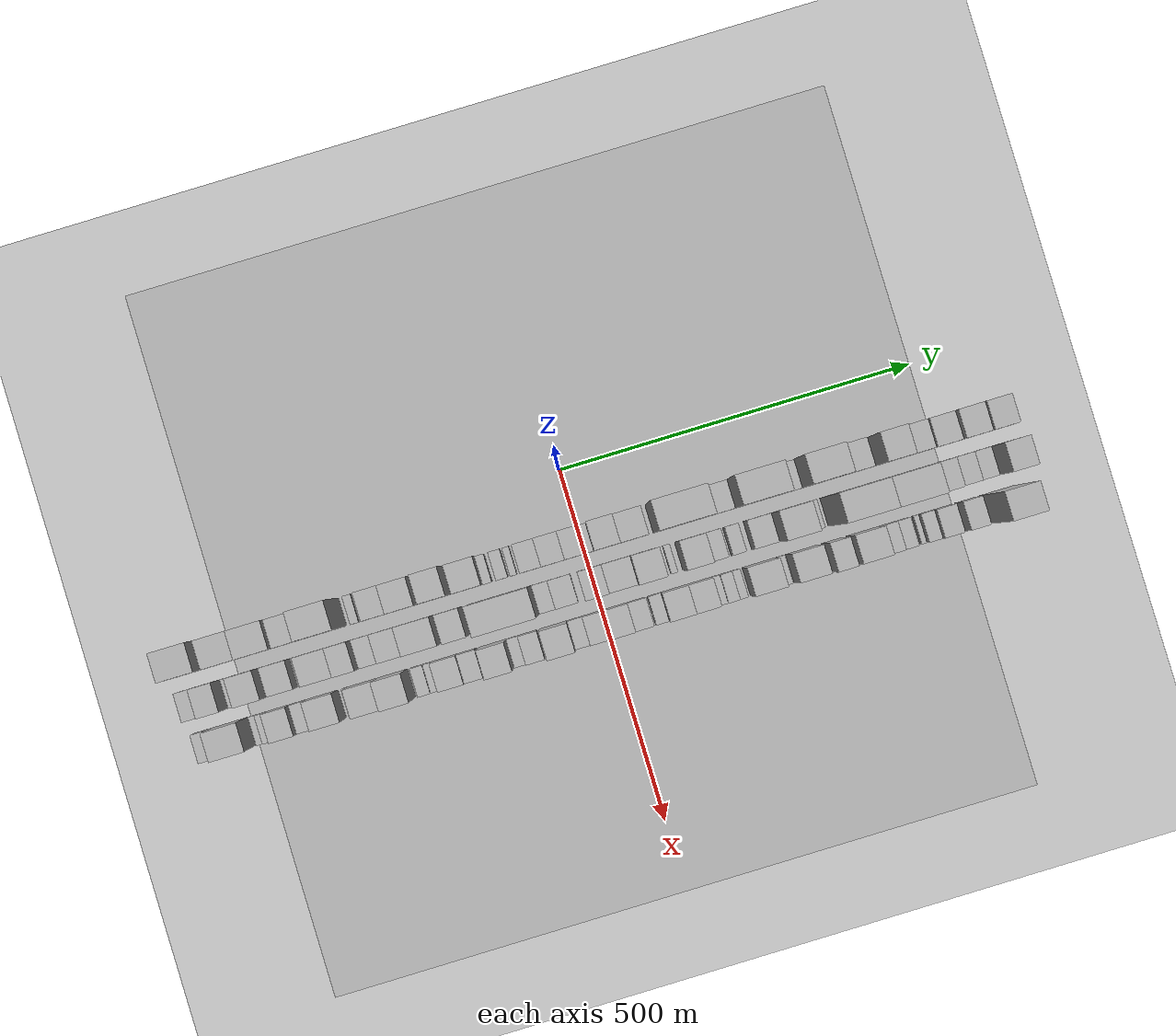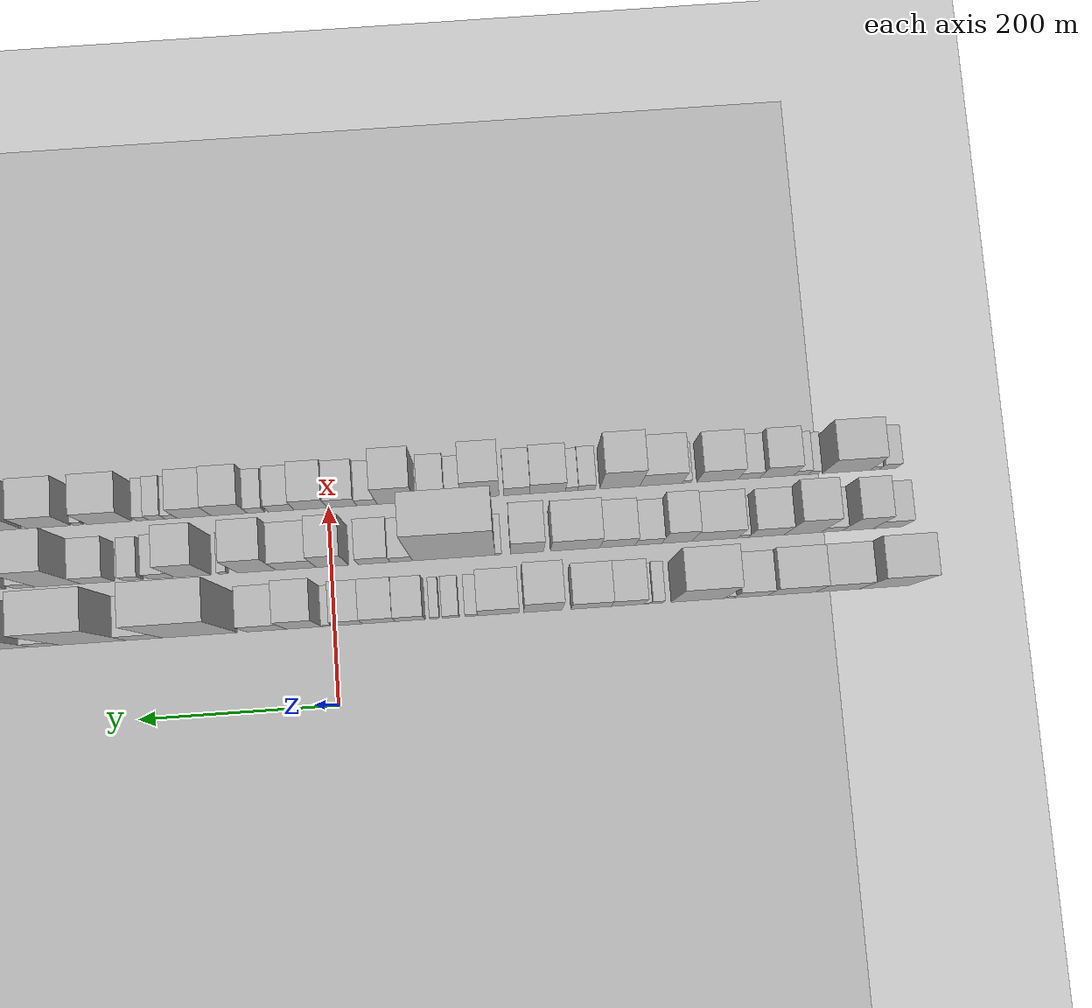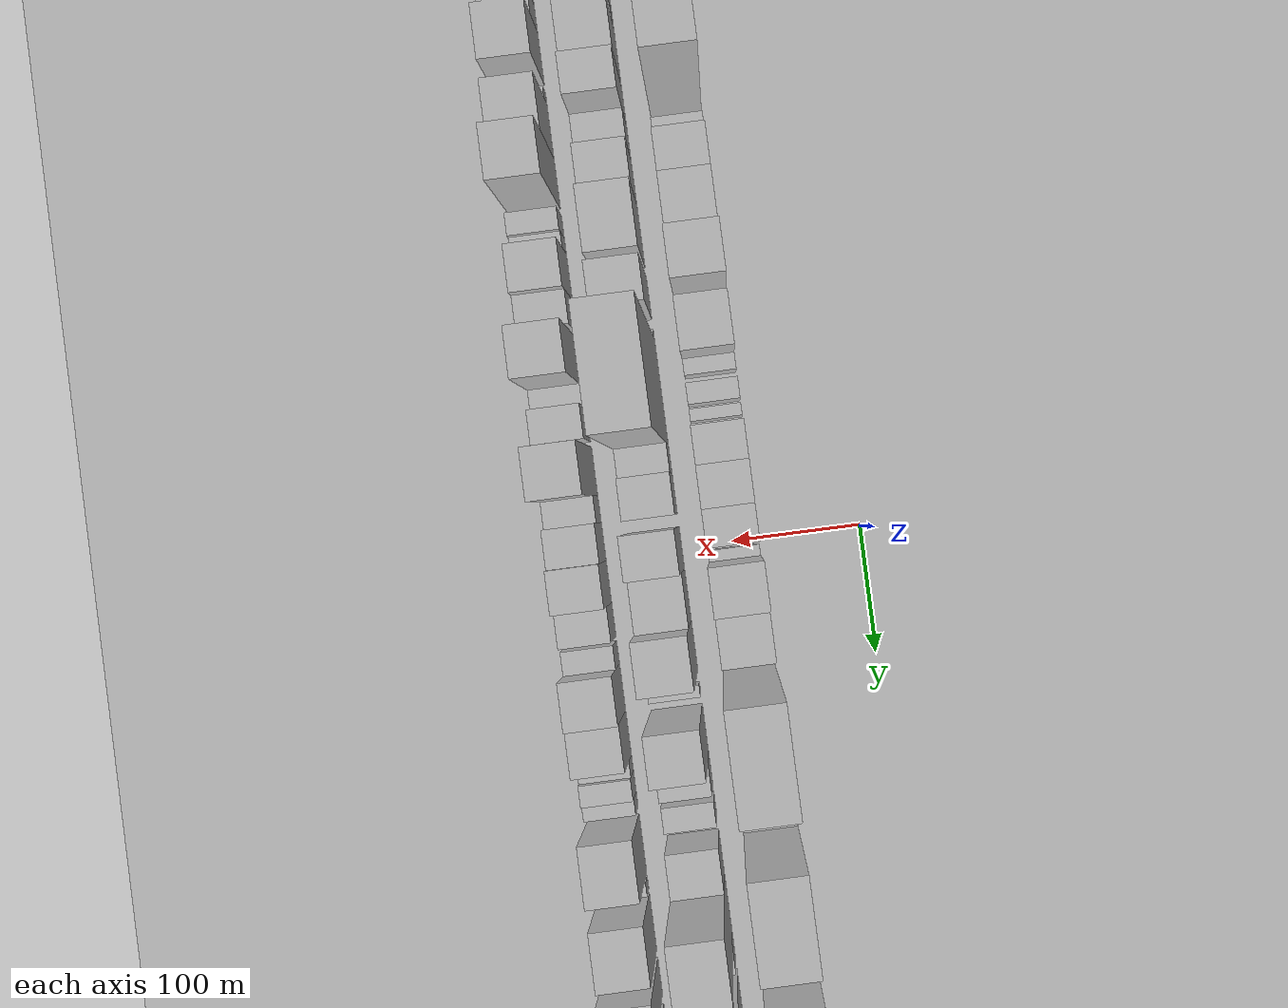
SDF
<?xml version="1.0" encoding="utf-8"?>

<sdf version="1.6">

   <world name="default">

      <gui fullscreen="0">

         <camera name="user_camera">

            <pose>-15 0 4.57585 0 0 0</pose>

            <view_controller>orbit</view_controller>

         </camera>

      </gui>

      <scene>

         <sky>

           <clouds>

             <speed>12</speed>

           </clouds>

         </sky>

         <ambient>0.4 0.4 0.4 1</ambient>

         <background>0.7 0.7 0.7 1</background>

         <shadows>1</shadows>

      </scene>

      <gravity>0 0 -9.8066</gravity>

      <magnetic_field>6e-06 2.3e-05 -4.2e-05</magnetic_field>

      <physics default="0" name="default_physics" type="ode">

         <ode>

            <solver>

               <type>quick</type>

               <iters>10</iters>

               <sor>1.0</sor>

               <use_dynamic_moi_rescaling>0</use_dynamic_moi_rescaling>

            </solver>

            <constraints>

               <cfm>0</cfm>

               <erp>0.2</erp>

               <contact_max_correcting_vel>100</contact_max_correcting_vel>

               <contact_surface_layer>0.001</contact_surface_layer>

            </constraints>

         </ode>

         <max_step_size>0.004</max_step_size>

         <real_time_factor>1</real_time_factor>

         <real_time_update_rate>250</real_time_update_rate>

      </physics>

      <light name="sun" type="directional">

         <cast_shadows>1</cast_shadows>

         <pose>0 0 10 0 0 0</pose>

         <diffuse>0.8 0.8 0.8 1</diffuse>

         <specular>0.2 0.2 0.2 1</specular>

         <attenuation>

            <range>1000</range>

            <constant>0.9</constant>

            <linear>0.01</linear>

            <quadratic>0.001</quadratic>

         </attenuation>

         <direction>-0.5 0.1 -0.9</direction>

      </light>

      <include>

         <name>ground_plane_1</name>

         <uri>model://HANNAS_ground_plane</uri>

         <pose>0 0 0  0 0 0</pose>

      </include>

      <include>

         <name>ground_plane_2</name>

         <uri>model://HANNAS_ground_plane</uri>

         <pose>100 0 0  0 0 0</pose>

      </include>

      <model name="building_1">

         <static>1</static>

         <pose frame="">100.0000 -554.9197 0 0.000000 0.000000 0.000000</pose>

         <link name="link">

            <pose frame="">0 0 64.50 0 0 0</pose>

            <collision name="collision">

               <geometry>

                  <box>

                     <size>40.0000 50.1606 129.0000</size>

                  </box>

               </geometry>

               <max_contacts>10</max_contacts>

               <surface>

                  <contact>

                     <ode/>

                  </contact>

                  <bounce/>

                  <friction>

                     <torsional>

                        <ode/>

                     </torsional>

                     <ode/>

                  </friction>

               </surface>

            </collision>

            <visual name="visual">

               <cast_shadows>0</cast_shadows>

               <geometry>

                  <box>

                     <size>40.0000 50.1606 129.0000</size>

                  </box>

               </geometry>

               <material>

                  <script>

                     <uri>model://HANNAS_wall/materials/scripts</uri>

                     <uri>model://HANNAS_wall/materials/textures</uri>

                     <name>vrc/HANNAS_wall</name>

                  </script>

               </material>

            </visual>

            <self_collide>0</self_collide>

            <enable_wind>0</enable_wind>

            <kinematic>0</kinematic>

         </link>

      </model>

      <model name="building_2">

         <static>1</static>

         <pose frame="">100.0000 -507.3606 0 0.000000 0.000000 0.000000</pose>

         <link name="link">

            <pose frame="">0 0 42.00 0 0 0</pose>

            <collision name="collision">

               <geometry>

                  <box>

                     <size>40.0000 44.9576 84.0000</size>

                  </box>

               </geometry>

               <max_contacts>10</max_contacts>

               <surface>

                  <contact>

                     <ode/>

                  </contact>

                  <bounce/>

                  <friction>

                     <torsional>

                        <ode/>

                     </torsional>

                     <ode/>

                  </friction>

               </surface>

            </collision>

            <visual name="visual">

               <cast_shadows>0</cast_shadows>

               <geometry>

                  <box>

                     <size>40.0000 44.9576 84.0000</size>

                  </box>

               </geometry>

               <material>

                  <script>

                     <uri>model://HANNAS_wall/materials/scripts</uri>

                     <uri>model://HANNAS_wall/materials/textures</uri>

                     <name>vrc/HANNAS_wall</name>

                  </script>

               </material>

            </visual>

            <self_collide>0</self_collide>

            <enable_wind>0</enable_wind>

            <kinematic>0</kinematic>

         </link>

      </model>

      <model name="building_3">

         <static>1</static>

         <pose frame="">100.0000 -460.6821 0 0.000000 0.000000 0.000000</pose>

         <link name="link">

            <pose frame="">0 0 42.00 0 0 0</pose>

            <collision name="collision">

               <geometry>

                  <box>

                     <size>40.0000 48.3995 84.0000</size>

                  </box>

               </geometry>

               <max_contacts>10</max_contacts>

               <surface>

                  <contact>

                     <ode/>

                  </contact>

                  <bounce/>

                  <friction>

                     <torsional>

                        <ode/>

                     </torsional>

                     <ode/>

                  </friction>

               </surface>

            </collision>

            <visual name="visual">

               <cast_shadows>0</cast_shadows>

               <geometry>

                  <box>

                     <size>40.0000 48.3995 84.0000</size>

                  </box>

               </geometry>

               <material>

                  <script>

                     <uri>model://HANNAS_wall/materials/scripts</uri>

                     <uri>model://HANNAS_wall/materials/textures</uri>

                     <name>vrc/HANNAS_wall</name>

                  </script>

               </material>

            </visual>

            <self_collide>0</self_collide>

            <enable_wind>0</enable_wind>

            <kinematic>0</kinematic>

         </link>

      </model>

      <model name="building_4">

         <static>1</static>

         <pose frame="">100.0000 -419.5346 0 0.000000 0.000000 0.000000</pose>

         <link name="link">

            <pose frame="">0 0 31.50 0 0 0</pose>

            <collision name="collision">

               <geometry>

                  <box>

                     <size>40.0000 33.8955 63.0000</size>

                  </box>

               </geometry>

               <max_contacts>10</max_contacts>

               <surface>

                  <contact>

                     <ode/>

                  </contact>

                  <bounce/>

                  <friction>

                     <torsional>

                        <ode/>

                     </torsional>

                     <ode/>

                  </friction>

               </surface>

            </collision>

            <visual name="visual">

               <cast_shadows>0</cast_shadows>

               <geometry>

                  <box>

                     <size>40.0000 33.8955 63.0000</size>

                  </box>

               </geometry>

               <material>

                  <script>

                     <uri>model://HANNAS_wall/materials/scripts</uri>

                     <uri>model://HANNAS_wall/materials/textures</uri>

                     <name>vrc/HANNAS_wall</name>

                  </script>

               </material>

            </visual>

            <self_collide>0</self_collide>

            <enable_wind>0</enable_wind>

            <kinematic>0</kinematic>

         </link>

      </model>

      <model name="building_5">

         <static>1</static>

         <pose frame="">100.0000 -397.4745 0 0.000000 0.000000 0.000000</pose>

         <link name="link">

            <pose frame="">0 0 12.00 0 0 0</pose>

            <collision name="collision">

               <geometry>

                  <box>

                     <size>40.0000 10.2246 24.0000</size>

                  </box>

               </geometry>

               <max_contacts>10</max_contacts>

               <surface>

                  <contact>

                     <ode/>

                  </contact>

                  <bounce/>

                  <friction>

                     <torsional>

                        <ode/>

                     </torsional>

                     <ode/>

                  </friction>

               </surface>

            </collision>

            <visual name="visual">

               <cast_shadows>0</cast_shadows>

               <geometry>

                  <box>

                     <size>40.0000 10.2246 24.0000</size>

                  </box>

               </geometry>

               <material>

                  <script>

                     <uri>model://HANNAS_wall/materials/scripts</uri>

                     <uri>model://HANNAS_wall/materials/textures</uri>

                     <name>vrc/HANNAS_wall</name>

                  </script>

               </material>

            </visual>

            <self_collide>0</self_collide>

            <enable_wind>0</enable_wind>

            <kinematic>0</kinematic>

         </link>

      </model>

      <model name="building_6">

         <static>1</static>

         <pose frame="">100.0000 -365.7914 0 0.000000 0.000000 0.000000</pose>

         <link name="link">

            <pose frame="">0 0 75.00 0 0 0</pose>

            <collision name="collision">

               <geometry>

                  <box>

                     <size>40.0000 53.1416 150.0000</size>

                  </box>

               </geometry>

               <max_contacts>10</max_contacts>

               <surface>

                  <contact>

                     <ode/>

                  </contact>

                  <bounce/>

                  <friction>

                     <torsional>

                        <ode/>

                     </torsional>

                     <ode/>

                  </friction>

               </surface>

            </collision>

            <visual name="visual">

               <cast_shadows>0</cast_shadows>

               <geometry>

                  <box>

                     <size>40.0000 53.1416 150.0000</size>

                  </box>

               </geometry>

               <material>

                  <script>

                     <uri>model://HANNAS_wall/materials/scripts</uri>

                     <uri>model://HANNAS_wall/materials/textures</uri>

                     <name>vrc/HANNAS_wall</name>

                  </script>

               </material>

            </visual>

            <self_collide>0</self_collide>

            <enable_wind>0</enable_wind>

            <kinematic>0</kinematic>

         </link>

      </model>

      <model name="building_7">

         <static>1</static>

         <pose frame="">100.0000 -325.1883 0 0.000000 0.000000 0.000000</pose>

         <link name="link">

            <pose frame="">0 0 13.50 0 0 0</pose>

            <collision name="collision">

               <geometry>

                  <box>

                     <size>40.0000 12.0646 27.0000</size>

                  </box>

               </geometry>

               <max_contacts>10</max_contacts>

               <surface>

                  <contact>

                     <ode/>

                  </contact>

                  <bounce/>

                  <friction>

                     <torsional>

                        <ode/>

                     </torsional>

                     <ode/>

                  </friction>

               </surface>

            </collision>

            <visual name="visual">

               <cast_shadows>0</cast_shadows>

               <geometry>

                  <box>

                     <size>40.0000 12.0646 27.0000</size>

                  </box>

               </geometry>

               <material>

                  <script>

                     <uri>model://HANNAS_wall/materials/scripts</uri>

                     <uri>model://HANNAS_wall/materials/textures</uri>

                     <name>vrc/HANNAS_wall</name>

                  </script>

               </material>

            </visual>

            <self_collide>0</self_collide>

            <enable_wind>0</enable_wind>

            <kinematic>0</kinematic>

         </link>

      </model>

      <model name="building_8">

         <static>1</static>

         <pose frame="">100.0000 -315.4075 0 0.000000 0.000000 0.000000</pose>

         <link name="link">

            <pose frame="">0 0 7.50 0 0 0</pose>

            <collision name="collision">

               <geometry>

                  <box>

                     <size>40.0000 7.4971 15.0000</size>

                  </box>

               </geometry>

               <max_contacts>10</max_contacts>

               <surface>

                  <contact>

                     <ode/>

                  </contact>

                  <bounce/>

                  <friction>

                     <torsional>

                        <ode/>

                     </torsional>

                     <ode/>

                  </friction>

               </surface>

            </collision>

            <visual name="visual">

               <cast_shadows>0</cast_shadows>

               <geometry>

                  <box>

                     <size>40.0000 7.4971 15.0000</size>

                  </box>

               </geometry>

               <material>

                  <script>

                     <uri>model://HANNAS_wall/materials/scripts</uri>

                     <uri>model://HANNAS_wall/materials/textures</uri>

                     <name>vrc/HANNAS_wall</name>

                  </script>

               </material>

            </visual>

            <self_collide>0</self_collide>

            <enable_wind>0</enable_wind>

            <kinematic>0</kinematic>

         </link>

      </model>

      <model name="building_9">

         <static>1</static>

         <pose frame="">100.0000 -294.9238 0 0.000000 0.000000 0.000000</pose>

         <link name="link">

            <pose frame="">0 0 33.00 0 0 0</pose>

            <collision name="collision">

               <geometry>

                  <box>

                     <size>40.0000 33.4705 66.0000</size>

                  </box>

               </geometry>

               <max_contacts>10</max_contacts>

               <surface>

                  <contact>

                     <ode/>

                  </contact>

                  <bounce/>

                  <friction>

                     <torsional>

                        <ode/>

                     </torsional>

                     <ode/>

                  </friction>

               </surface>

            </collision>

            <visual name="visual">

               <cast_shadows>0</cast_shadows>

               <geometry>

                  <box>

                     <size>40.0000 33.4705 66.0000</size>

                  </box>

               </geometry>

               <material>

                  <script>

                     <uri>model://HANNAS_wall/materials/scripts</uri>

                     <uri>model://HANNAS_wall/materials/textures</uri>

                     <name>vrc/HANNAS_wall</name>

                  </script>

               </material>

            </visual>

            <self_collide>0</self_collide>

            <enable_wind>0</enable_wind>

            <kinematic>0</kinematic>

         </link>

      </model>

      <model name="building_10">

         <static>1</static>

         <pose frame="">100.0000 -257.9560 0 0.000000 0.000000 0.000000</pose>

         <link name="link">

            <pose frame="">0 0 34.50 0 0 0</pose>

            <collision name="collision">

               <geometry>

                  <box>

                     <size>40.0000 40.4650 69.0000</size>

                  </box>

               </geometry>

               <max_contacts>10</max_contacts>

               <surface>

                  <contact>

                     <ode/>

                  </contact>

                  <bounce/>

                  <friction>

                     <torsional>

                        <ode/>

                     </torsional>

                     <ode/>

                  </friction>

               </surface>

            </collision>

            <visual name="visual">

               <cast_shadows>0</cast_shadows>

               <geometry>

                  <box>

                     <size>40.0000 40.4650 69.0000</size>

                  </box>

               </geometry>

               <material>

                  <script>

                     <uri>model://HANNAS_wall/materials/scripts</uri>

                     <uri>model://HANNAS_wall/materials/textures</uri>

                     <name>vrc/HANNAS_wall</name>

                  </script>

               </material>

            </visual>

            <self_collide>0</self_collide>

            <enable_wind>0</enable_wind>

            <kinematic>0</kinematic>

         </link>

      </model>

      <model name="building_11">

         <static>1</static>

         <pose frame="">100.0000 -209.4737 0 0.000000 0.000000 0.000000</pose>

         <link name="link">

            <pose frame="">0 0 57.00 0 0 0</pose>

            <collision name="collision">

               <geometry>

                  <box>

                     <size>40.0000 38.4995 114.0000</size>

                  </box>

               </geometry>

               <max_contacts>10</max_contacts>

               <surface>

                  <contact>

                     <ode/>

                  </contact>

                  <bounce/>

                  <friction>

                     <torsional>

                        <ode/>

                     </torsional>

                     <ode/>

                  </friction>

               </surface>

            </collision>

            <visual name="visual">

               <cast_shadows>0</cast_shadows>

               <geometry>

                  <box>

                     <size>40.0000 38.4995 114.0000</size>

                  </box>

               </geometry>

               <material>

                  <script>

                     <uri>model://HANNAS_wall/materials/scripts</uri>

                     <uri>model://HANNAS_wall/materials/textures</uri>

                     <name>vrc/HANNAS_wall</name>

                  </script>

               </material>

            </visual>

            <self_collide>0</self_collide>

            <enable_wind>0</enable_wind>

            <kinematic>0</kinematic>

         </link>

      </model>

      <model name="building_12">

         <static>1</static>

         <pose frame="">100.0000 -164.6965 0 0.000000 0.000000 0.000000</pose>

         <link name="link">

            <pose frame="">0 0 37.50 0 0 0</pose>

            <collision name="collision">

               <geometry>

                  <box>

                     <size>40.0000 41.0549 75.0000</size>

                  </box>

               </geometry>

               <max_contacts>10</max_contacts>

               <surface>

                  <contact>

                     <ode/>

                  </contact>

                  <bounce/>

                  <friction>

                     <torsional>

                        <ode/>

                     </torsional>

                     <ode/>

                  </friction>

               </surface>

            </collision>

            <visual name="visual">

               <cast_shadows>0</cast_shadows>

               <geometry>

                  <box>

                     <size>40.0000 41.0549 75.0000</size>

                  </box>

               </geometry>

               <material>

                  <script>

                     <uri>model://HANNAS_wall/materials/scripts</uri>

                     <uri>model://HANNAS_wall/materials/textures</uri>

                     <name>vrc/HANNAS_wall</name>

                  </script>

               </material>

            </visual>

            <self_collide>0</self_collide>

            <enable_wind>0</enable_wind>

            <kinematic>0</kinematic>

         </link>

      </model>

      <model name="building_13">

         <static>1</static>

         <pose frame="">100.0000 -137.7292 0 0.000000 0.000000 0.000000</pose>

         <link name="link">

            <pose frame="">0 0 13.50 0 0 0</pose>

            <collision name="collision">

               <geometry>

                  <box>

                     <size>40.0000 12.8798 27.0000</size>

                  </box>

               </geometry>

               <max_contacts>10</max_contacts>

               <surface>

                  <contact>

                     <ode/>

                  </contact>

                  <bounce/>

                  <friction>

                     <torsional>

                        <ode/>

                     </torsional>

                     <ode/>

                  </friction>

               </surface>

            </collision>

            <visual name="visual">

               <cast_shadows>0</cast_shadows>

               <geometry>

                  <box>

                     <size>40.0000 12.8798 27.0000</size>

                  </box>

               </geometry>

               <material>

                  <script>

                     <uri>model://HANNAS_wall/materials/scripts</uri>

                     <uri>model://HANNAS_wall/materials/textures</uri>

                     <name>vrc/HANNAS_wall</name>

                  </script>

               </material>

            </visual>

            <self_collide>0</self_collide>

            <enable_wind>0</enable_wind>

            <kinematic>0</kinematic>

         </link>

      </model>

      <model name="building_14">

         <static>1</static>

         <pose frame="">100.0000 -116.9414 0 0.000000 0.000000 0.000000</pose>

         <link name="link">

            <pose frame="">0 0 15.00 0 0 0</pose>

            <collision name="collision">

               <geometry>

                  <box>

                     <size>40.0000 16.6959 30.0000</size>

                  </box>

               </geometry>

               <max_contacts>10</max_contacts>

               <surface>

                  <contact>

                     <ode/>

                  </contact>

                  <bounce/>

                  <friction>

                     <torsional>

                        <ode/>

                     </torsional>

                     <ode/>

                  </friction>

               </surface>

            </collision>

            <visual name="visual">

               <cast_shadows>0</cast_shadows>

               <geometry>

                  <box>

                     <size>40.0000 16.6959 30.0000</size>

                  </box>

               </geometry>

               <material>

                  <script>

                     <uri>model://HANNAS_wall/materials/scripts</uri>

                     <uri>model://HANNAS_wall/materials/textures</uri>

                     <name>vrc/HANNAS_wall</name>

                  </script>

               </material>

            </visual>

            <self_collide>0</self_collide>

            <enable_wind>0</enable_wind>

            <kinematic>0</kinematic>

         </link>

      </model>

      <model name="building_15">

         <static>1</static>

         <pose frame="">100.0000 -100.7595 0 0.000000 0.000000 0.000000</pose>

         <link name="link">

            <pose frame="">0 0 12.00 0 0 0</pose>

            <collision name="collision">

               <geometry>

                  <box>

                     <size>40.0000 9.6678 24.0000</size>

                  </box>

               </geometry>

               <max_contacts>10</max_contacts>

               <surface>

                  <contact>

                     <ode/>

                  </contact>

                  <bounce/>

                  <friction>

                     <torsional>

                        <ode/>

                     </torsional>

                     <ode/>

                  </friction>

               </surface>

            </collision>

            <visual name="visual">

               <cast_shadows>0</cast_shadows>

               <geometry>

                  <box>

                     <size>40.0000 9.6678 24.0000</size>

                  </box>

               </geometry>

               <material>

                  <script>

                     <uri>model://HANNAS_wall/materials/scripts</uri>

                     <uri>model://HANNAS_wall/materials/textures</uri>

                     <name>vrc/HANNAS_wall</name>

                  </script>

               </material>

            </visual>

            <self_collide>0</self_collide>

            <enable_wind>0</enable_wind>

            <kinematic>0</kinematic>

         </link>

      </model>

      <model name="building_16">

         <static>1</static>

         <pose frame="">100.0000 -75.9965 0 0.000000 0.000000 0.000000</pose>

         <link name="link">

            <pose frame="">0 0 28.50 0 0 0</pose>

            <collision name="collision">

               <geometry>

                  <box>

                     <size>40.0000 29.8584 57.0000</size>

                  </box>

               </geometry>

               <max_contacts>10</max_contacts>

               <surface>

                  <contact>

                     <ode/>

                  </contact>

                  <bounce/>

                  <friction>

                     <torsional>

                        <ode/>

                     </torsional>

                     <ode/>

                  </friction>

               </surface>

            </collision>

            <visual name="visual">

               <cast_shadows>0</cast_shadows>

               <geometry>

                  <box>

                     <size>40.0000 29.8584 57.0000</size>

                  </box>

               </geometry>

               <material>

                  <script>

                     <uri>model://HANNAS_wall/materials/scripts</uri>

                     <uri>model://HANNAS_wall/materials/textures</uri>

                     <name>vrc/HANNAS_wall</name>

                  </script>

               </material>

            </visual>

            <self_collide>0</self_collide>

            <enable_wind>0</enable_wind>

            <kinematic>0</kinematic>

         </link>

      </model>

      <model name="building_17">

         <static>1</static>

         <pose frame="">100.0000 -44.6055 0 0.000000 0.000000 0.000000</pose>

         <link name="link">

            <pose frame="">0 0 30.00 0 0 0</pose>

            <collision name="collision">

               <geometry>

                  <box>

                     <size>40.0000 32.9234 60.0000</size>

                  </box>

               </geometry>

               <max_contacts>10</max_contacts>

               <surface>

                  <contact>

                     <ode/>

                  </contact>

                  <bounce/>

                  <friction>

                     <torsional>

                        <ode/>

                     </torsional>

                     <ode/>

                  </friction>

               </surface>

            </collision>

            <visual name="visual">

               <cast_shadows>0</cast_shadows>

               <geometry>

                  <box>

                     <size>40.0000 32.9234 60.0000</size>

                  </box>

               </geometry>

               <material>

                  <script>

                     <uri>model://HANNAS_wall/materials/scripts</uri>

                     <uri>model://HANNAS_wall/materials/textures</uri>

                     <name>vrc/HANNAS_wall</name>

                  </script>

               </material>

            </visual>

            <self_collide>0</self_collide>

            <enable_wind>0</enable_wind>

            <kinematic>0</kinematic>

         </link>

      </model>

      <model name="building_18">

         <static>1</static>

         <pose frame="">100.0000 -13.6003 0 0.000000 0.000000 0.000000</pose>

         <link name="link">

            <pose frame="">0 0 28.50 0 0 0</pose>

            <collision name="collision">

               <geometry>

                  <box>

                     <size>40.0000 29.0871 57.0000</size>

                  </box>

               </geometry>

               <max_contacts>10</max_contacts>

               <surface>

                  <contact>

                     <ode/>

                  </contact>

                  <bounce/>

                  <friction>

                     <torsional>

                        <ode/>

                     </torsional>

                     <ode/>

                  </friction>

               </surface>

            </collision>

            <visual name="visual">

               <cast_shadows>0</cast_shadows>

               <geometry>

                  <box>

                     <size>40.0000 29.0871 57.0000</size>

                  </box>

               </geometry>

               <material>

                  <script>

                     <uri>model://HANNAS_wall/materials/scripts</uri>

                     <uri>model://HANNAS_wall/materials/textures</uri>

                     <name>vrc/HANNAS_wall</name>

                  </script>

               </material>

            </visual>

            <self_collide>0</self_collide>

            <enable_wind>0</enable_wind>

            <kinematic>0</kinematic>

         </link>

      </model>

      <model name="building_19">

         <static>1</static>

         <pose frame="">100.0000 8.3785 0 0.000000 0.000000 0.000000</pose>

         <link name="link">

            <pose frame="">0 0 9.00 0 0 0</pose>

            <collision name="collision">

               <geometry>

                  <box>

                     <size>40.0000 8.8705 18.0000</size>

                  </box>

               </geometry>

               <max_contacts>10</max_contacts>

               <surface>

                  <contact>

                     <ode/>

                  </contact>

                  <bounce/>

                  <friction>

                     <torsional>

                        <ode/>

                     </torsional>

                     <ode/>

                  </friction>

               </surface>

            </collision>

            <visual name="visual">

               <cast_shadows>0</cast_shadows>

               <geometry>

                  <box>

                     <size>40.0000 8.8705 18.0000</size>

                  </box>

               </geometry>

               <material>

                  <script>

                     <uri>model://HANNAS_wall/materials/scripts</uri>

                     <uri>model://HANNAS_wall/materials/textures</uri>

                     <name>vrc/HANNAS_wall</name>

                  </script>

               </material>

            </visual>

            <self_collide>0</self_collide>

            <enable_wind>0</enable_wind>

            <kinematic>0</kinematic>

         </link>

      </model>

      <model name="building_20">

         <static>1</static>

         <pose frame="">100.0000 30.8824 0 0.000000 0.000000 0.000000</pose>

         <link name="link">

            <pose frame="">0 0 54.00 0 0 0</pose>

            <collision name="collision">

               <geometry>

                  <box>

                     <size>40.0000 36.1372 108.0000</size>

                  </box>

               </geometry>

               <max_contacts>10</max_contacts>

               <surface>

                  <contact>

                     <ode/>

                  </contact>

                  <bounce/>

                  <friction>

                     <torsional>

                        <ode/>

                     </torsional>

                     <ode/>

                  </friction>

               </surface>

            </collision>

            <visual name="visual">

               <cast_shadows>0</cast_shadows>

               <geometry>

                  <box>

                     <size>40.0000 36.1372 108.0000</size>

                  </box>

               </geometry>

               <material>

                  <script>

                     <uri>model://HANNAS_wall/materials/scripts</uri>

                     <uri>model://HANNAS_wall/materials/textures</uri>

                     <name>vrc/HANNAS_wall</name>

                  </script>

               </material>

            </visual>

            <self_collide>0</self_collide>

            <enable_wind>0</enable_wind>

            <kinematic>0</kinematic>

         </link>

      </model>

      <model name="building_21">

         <static>1</static>

         <pose frame="">100.0000 68.9790 0 0.000000 0.000000 0.000000</pose>

         <link name="link">

            <pose frame="">0 0 37.50 0 0 0</pose>

            <collision name="collision">

               <geometry>

                  <box>

                     <size>40.0000 40.0560 75.0000</size>

                  </box>

               </geometry>

               <max_contacts>10</max_contacts>

               <surface>

                  <contact>

                     <ode/>

                  </contact>

                  <bounce/>

                  <friction>

                     <torsional>

                        <ode/>

                     </torsional>

                     <ode/>

                  </friction>

               </surface>

            </collision>

            <visual name="visual">

               <cast_shadows>0</cast_shadows>

               <geometry>

                  <box>

                     <size>40.0000 40.0560 75.0000</size>

                  </box>

               </geometry>

               <material>

                  <script>

                     <uri>model://HANNAS_wall/materials/scripts</uri>

                     <uri>model://HANNAS_wall/materials/textures</uri>

                     <name>vrc/HANNAS_wall</name>

                  </script>

               </material>

            </visual>

            <self_collide>0</self_collide>

            <enable_wind>0</enable_wind>

            <kinematic>0</kinematic>

         </link>

      </model>

      <model name="building_22">

         <static>1</static>

         <pose frame="">100.0000 135.8817 0 0.000000 0.000000 0.000000</pose>

         <link name="link">

            <pose frame="">0 0 97.50 0 0 0</pose>

            <collision name="collision">

               <geometry>

                  <box>

                     <size>40.0000 75.7494 195.0000</size>

                  </box>

               </geometry>

               <max_contacts>10</max_contacts>

               <surface>

                  <contact>

                     <ode/>

                  </contact>

                  <bounce/>

                  <friction>

                     <torsional>

                        <ode/>

                     </torsional>

                     <ode/>

                  </friction>

               </surface>

            </collision>

            <visual name="visual">

               <cast_shadows>0</cast_shadows>

               <geometry>

                  <box>

                     <size>40.0000 75.7494 195.0000</size>

                  </box>

               </geometry>

               <material>

                  <script>

                     <uri>model://HANNAS_wall/materials/scripts</uri>

                     <uri>model://HANNAS_wall/materials/textures</uri>

                     <name>vrc/HANNAS_wall</name>

                  </script>

               </material>

            </visual>

            <self_collide>0</self_collide>

            <enable_wind>0</enable_wind>

            <kinematic>0</kinematic>

         </link>

      </model>

      <model name="building_23">

         <static>1</static>

         <pose frame="">100.0000 191.7278 0 0.000000 0.000000 0.000000</pose>

         <link name="link">

            <pose frame="">0 0 31.50 0 0 0</pose>

            <collision name="collision">

               <geometry>

                  <box>

                     <size>40.0000 35.9429 63.0000</size>

                  </box>

               </geometry>

               <max_contacts>10</max_contacts>

               <surface>

                  <contact>

                     <ode/>

                  </contact>

                  <bounce/>

                  <friction>

                     <torsional>

                        <ode/>

                     </torsional>

                     <ode/>

                  </friction>

               </surface>

            </collision>

            <visual name="visual">

               <cast_shadows>0</cast_shadows>

               <geometry>

                  <box>

                     <size>40.0000 35.9429 63.0000</size>

                  </box>

               </geometry>

               <material>

                  <script>

                     <uri>model://HANNAS_wall/materials/scripts</uri>

                     <uri>model://HANNAS_wall/materials/textures</uri>

                     <name>vrc/HANNAS_wall</name>

                  </script>

               </material>

            </visual>

            <self_collide>0</self_collide>

            <enable_wind>0</enable_wind>

            <kinematic>0</kinematic>

         </link>

      </model>

      <model name="building_24">

         <static>1</static>

         <pose frame="">100.0000 243.2532 0 0.000000 0.000000 0.000000</pose>

         <link name="link">

            <pose frame="">0 0 91.50 0 0 0</pose>

            <collision name="collision">

               <geometry>

                  <box>

                     <size>40.0000 67.1081 183.0000</size>

                  </box>

               </geometry>

               <max_contacts>10</max_contacts>

               <surface>

                  <contact>

                     <ode/>

                  </contact>

                  <bounce/>

                  <friction>

                     <torsional>

                        <ode/>

                     </torsional>

                     <ode/>

                  </friction>

               </surface>

            </collision>

            <visual name="visual">

               <cast_shadows>0</cast_shadows>

               <geometry>

                  <box>

                     <size>40.0000 67.1081 183.0000</size>

                  </box>

               </geometry>

               <material>

                  <script>

                     <uri>model://HANNAS_wall/materials/scripts</uri>

                     <uri>model://HANNAS_wall/materials/textures</uri>

                     <name>vrc/HANNAS_wall</name>

                  </script>

               </material>

            </visual>

            <self_collide>0</self_collide>

            <enable_wind>0</enable_wind>

            <kinematic>0</kinematic>

         </link>

      </model>

      <model name="building_25">

         <static>1</static>

         <pose frame="">100.0000 290.9221 0 0.000000 0.000000 0.000000</pose>

         <link name="link">

            <pose frame="">0 0 24.00 0 0 0</pose>

            <collision name="collision">

               <geometry>

                  <box>

                     <size>40.0000 28.2296 48.0000</size>

                  </box>

               </geometry>

               <max_contacts>10</max_contacts>

               <surface>

                  <contact>

                     <ode/>

                  </contact>

                  <bounce/>

                  <friction>

                     <torsional>

                        <ode/>

                     </torsional>

                     <ode/>

                  </friction>

               </surface>

            </collision>

            <visual name="visual">

               <cast_shadows>0</cast_shadows>

               <geometry>

                  <box>

                     <size>40.0000 28.2296 48.0000</size>

                  </box>

               </geometry>

               <material>

                  <script>

                     <uri>model://HANNAS_wall/materials/scripts</uri>

                     <uri>model://HANNAS_wall/materials/textures</uri>

                     <name>vrc/HANNAS_wall</name>

                  </script>

               </material>

            </visual>

            <self_collide>0</self_collide>

            <enable_wind>0</enable_wind>

            <kinematic>0</kinematic>

         </link>

      </model>

      <model name="building_26">

         <static>1</static>

         <pose frame="">100.0000 333.1549 0 0.000000 0.000000 0.000000</pose>

         <link name="link">

            <pose frame="">0 0 81.00 0 0 0</pose>

            <collision name="collision">

               <geometry>

                  <box>

                     <size>40.0000 56.2360 162.0000</size>

                  </box>

               </geometry>

               <max_contacts>10</max_contacts>

               <surface>

                  <contact>

                     <ode/>

                  </contact>

                  <bounce/>

                  <friction>

                     <torsional>

                        <ode/>

                     </torsional>

                     <ode/>

                  </friction>

               </surface>

            </collision>

            <visual name="visual">

               <cast_shadows>0</cast_shadows>

               <geometry>

                  <box>

                     <size>40.0000 56.2360 162.0000</size>

                  </box>

               </geometry>

               <material>

                  <script>

                     <uri>model://HANNAS_wall/materials/scripts</uri>

                     <uri>model://HANNAS_wall/materials/textures</uri>

                     <name>vrc/HANNAS_wall</name>

                  </script>

               </material>

            </visual>

            <self_collide>0</self_collide>

            <enable_wind>0</enable_wind>

            <kinematic>0</kinematic>

         </link>

      </model>

      <model name="building_27">

         <static>1</static>

         <pose frame="">100.0000 384.6901 0 0.000000 0.000000 0.000000</pose>

         <link name="link">

            <pose frame="">0 0 34.50 0 0 0</pose>

            <collision name="collision">

               <geometry>

                  <box>

                     <size>40.0000 38.8345 69.0000</size>

                  </box>

               </geometry>

               <max_contacts>10</max_contacts>

               <surface>

                  <contact>

                     <ode/>

                  </contact>

                  <bounce/>

                  <friction>

                     <torsional>

                        <ode/>

                     </torsional>

                     <ode/>

                  </friction>

               </surface>

            </collision>

            <visual name="visual">

               <cast_shadows>0</cast_shadows>

               <geometry>

                  <box>

                     <size>40.0000 38.8345 69.0000</size>

                  </box>

               </geometry>

               <material>

                  <script>

                     <uri>model://HANNAS_wall/materials/scripts</uri>

                     <uri>model://HANNAS_wall/materials/textures</uri>

                     <name>vrc/HANNAS_wall</name>

                  </script>

               </material>

            </visual>

            <self_collide>0</self_collide>

            <enable_wind>0</enable_wind>

            <kinematic>0</kinematic>

         </link>

      </model>

      <model name="building_28">

         <static>1</static>

         <pose frame="">100.0000 408.3020 0 0.000000 0.000000 0.000000</pose>

         <link name="link">

            <pose frame="">0 0 9.00 0 0 0</pose>

            <collision name="collision">

               <geometry>

                  <box>

                     <size>40.0000 8.3891 18.0000</size>

                  </box>

               </geometry>

               <max_contacts>10</max_contacts>

               <surface>

                  <contact>

                     <ode/>

                  </contact>

                  <bounce/>

                  <friction>

                     <torsional>

                        <ode/>

                     </torsional>

                     <ode/>

                  </friction>

               </surface>

            </collision>

            <visual name="visual">

               <cast_shadows>0</cast_shadows>

               <geometry>

                  <box>

                     <size>40.0000 8.3891 18.0000</size>

                  </box>

               </geometry>

               <material>

                  <script>

                     <uri>model://HANNAS_wall/materials/scripts</uri>

                     <uri>model://HANNAS_wall/materials/textures</uri>

                     <name>vrc/HANNAS_wall</name>

                  </script>

               </material>

            </visual>

            <self_collide>0</self_collide>

            <enable_wind>0</enable_wind>

            <kinematic>0</kinematic>

         </link>

      </model>

      <model name="building_29">

         <static>1</static>

         <pose frame="">100.0000 431.8983 0 0.000000 0.000000 0.000000</pose>

         <link name="link">

            <pose frame="">0 0 61.50 0 0 0</pose>

            <collision name="collision">

               <geometry>

                  <box>

                     <size>40.0000 38.8036 123.0000</size>

                  </box>

               </geometry>

               <max_contacts>10</max_contacts>

               <surface>

                  <contact>

                     <ode/>

                  </contact>

                  <bounce/>

                  <friction>

                     <torsional>

                        <ode/>

                     </torsional>

                     <ode/>

                  </friction>

               </surface>

            </collision>

            <visual name="visual">

               <cast_shadows>0</cast_shadows>

               <geometry>

                  <box>

                     <size>40.0000 38.8036 123.0000</size>

                  </box>

               </geometry>

               <material>

                  <script>

                     <uri>model://HANNAS_wall/materials/scripts</uri>

                     <uri>model://HANNAS_wall/materials/textures</uri>

                     <name>vrc/HANNAS_wall</name>

                  </script>

               </material>

            </visual>

            <self_collide>0</self_collide>

            <enable_wind>0</enable_wind>

            <kinematic>0</kinematic>

         </link>

      </model>

      <model name="building_30">

         <static>1</static>

         <pose frame="">100.0000 469.7049 0 0.000000 0.000000 0.000000</pose>

         <link name="link">

            <pose frame="">0 0 36.00 0 0 0</pose>

            <collision name="collision">

               <geometry>

                  <box>

                     <size>40.0000 36.8095 72.0000</size>

                  </box>

               </geometry>

               <max_contacts>10</max_contacts>

               <surface>

                  <contact>

                     <ode/>

                  </contact>

                  <bounce/>

                  <friction>

                     <torsional>

                        <ode/>

                     </torsional>

                     <ode/>

                  </friction>

               </surface>

            </collision>

            <visual name="visual">

               <cast_shadows>0</cast_shadows>

               <geometry>

                  <box>

                     <size>40.0000 36.8095 72.0000</size>

                  </box>

               </geometry>

               <material>

                  <script>

                     <uri>model://HANNAS_wall/materials/scripts</uri>

                     <uri>model://HANNAS_wall/materials/textures</uri>

                     <name>vrc/HANNAS_wall</name>

                  </script>

               </material>

            </visual>

            <self_collide>0</self_collide>

            <enable_wind>0</enable_wind>

            <kinematic>0</kinematic>

         </link>

      </model>

      <model name="building_31">

         <static>1</static>

         <pose frame="">100.0000 510.0738 0 0.000000 0.000000 0.000000</pose>

         <link name="link">

            <pose frame="">0 0 31.50 0 0 0</pose>

            <collision name="collision">

               <geometry>

                  <box>

                     <size>40.0000 35.9283 63.0000</size>

                  </box>

               </geometry>

               <max_contacts>10</max_contacts>

               <surface>

                  <contact>

                     <ode/>

                  </contact>

                  <bounce/>

                  <friction>

                     <torsional>

                        <ode/>

                     </torsional>

                     <ode/>

                  </friction>

               </surface>

            </collision>

            <visual name="visual">

               <cast_shadows>0</cast_shadows>

               <geometry>

                  <box>

                     <size>40.0000 35.9283 63.0000</size>

                  </box>

               </geometry>

               <material>

                  <script>

                     <uri>model://HANNAS_wall/materials/scripts</uri>

                     <uri>model://HANNAS_wall/materials/textures</uri>

                     <name>vrc/HANNAS_wall</name>

                  </script>

               </material>

            </visual>

            <self_collide>0</self_collide>

            <enable_wind>0</enable_wind>

            <kinematic>0</kinematic>

         </link>

      </model>

      <model name="building_32">

         <static>1</static>

         <pose frame="">100.0000 549.5832 0 0.000000 0.000000 0.000000</pose>

         <link name="link">

            <pose frame="">0 0 34.50 0 0 0</pose>

            <collision name="collision">

               <geometry>

                  <box>

                     <size>40.0000 37.0906 69.0000</size>

                  </box>

               </geometry>

               <max_contacts>10</max_contacts>

               <surface>

                  <contact>

                     <ode/>

                  </contact>

                  <bounce/>

                  <friction>

                     <torsional>

                        <ode/>

                     </torsional>

                     <ode/>

                  </friction>

               </surface>

            </collision>

            <visual name="visual">

               <cast_shadows>0</cast_shadows>

               <geometry>

                  <box>

                     <size>40.0000 37.0906 69.0000</size>

                  </box>

               </geometry>

               <material>

                  <script>

                     <uri>model://HANNAS_wall/materials/scripts</uri>

                     <uri>model://HANNAS_wall/materials/textures</uri>

                     <name>vrc/HANNAS_wall</name>

                  </script>

               </material>

            </visual>

            <self_collide>0</self_collide>

            <enable_wind>0</enable_wind>

            <kinematic>0</kinematic>

         </link>

      </model>

      <model name="building_33">

         <static>1</static>

         <pose frame="">100.0000 588.9337 0 0.000000 0.000000 0.000000</pose>

         <link name="link">

            <pose frame="">0 0 33.00 0 0 0</pose>

            <collision name="collision">

               <geometry>

                  <box>

                     <size>40.0000 35.6104 66.0000</size>

                  </box>

               </geometry>

               <max_contacts>10</max_contacts>

               <surface>

                  <contact>

                     <ode/>

                  </contact>

                  <bounce/>

                  <friction>

                     <torsional>

                        <ode/>

                     </torsional>

                     <ode/>

                  </friction>

               </surface>

            </collision>

            <visual name="visual">

               <cast_shadows>0</cast_shadows>

               <geometry>

                  <box>

                     <size>40.0000 35.6104 66.0000</size>

                  </box>

               </geometry>

               <material>

                  <script>

                     <uri>model://HANNAS_wall/materials/scripts</uri>

                     <uri>model://HANNAS_wall/materials/textures</uri>

                     <name>vrc/HANNAS_wall</name>

                  </script>

               </material>

            </visual>

            <self_collide>0</self_collide>

            <enable_wind>0</enable_wind>

            <kinematic>0</kinematic>

         </link>

      </model>

      <model name="building_34">

         <static>1</static>

         <pose frame="">160.0000 -565.0322 0 0.000000 0.000000 0.000000</pose>

         <link name="link">

            <pose frame="">0 0 28.50 0 0 0</pose>

            <collision name="collision">

               <geometry>

                  <box>

                     <size>40.0000 29.9356 57.0000</size>

                  </box>

               </geometry>

               <max_contacts>10</max_contacts>

               <surface>

                  <contact>

                     <ode/>

                  </contact>

                  <bounce/>

                  <friction>

                     <torsional>

                        <ode/>

                     </torsional>

                     <ode/>

                  </friction>

               </surface>

            </collision>

            <visual name="visual">

               <cast_shadows>0</cast_shadows>

               <geometry>

                  <box>

                     <size>40.0000 29.9356 57.0000</size>

                  </box>

               </geometry>

               <material>

                  <script>

                     <uri>model://HANNAS_wall/materials/scripts</uri>

                     <uri>model://HANNAS_wall/materials/textures</uri>

                     <name>vrc/HANNAS_wall</name>

                  </script>

               </material>

            </visual>

            <self_collide>0</self_collide>

            <enable_wind>0</enable_wind>

            <kinematic>0</kinematic>

         </link>

      </model>

      <model name="building_35">

         <static>1</static>

         <pose frame="">160.0000 -534.2902 0 0.000000 0.000000 0.000000</pose>

         <link name="link">

            <pose frame="">0 0 51.00 0 0 0</pose>

            <collision name="collision">

               <geometry>

                  <box>

                     <size>40.0000 31.5484 102.0000</size>

                  </box>

               </geometry>

               <max_contacts>10</max_contacts>

               <surface>

                  <contact>

                     <ode/>

                  </contact>

                  <bounce/>

                  <friction>

                     <torsional>

                        <ode/>

                     </torsional>

                     <ode/>

                  </friction>

               </surface>

            </collision>

            <visual name="visual">

               <cast_shadows>0</cast_shadows>

               <geometry>

                  <box>

                     <size>40.0000 31.5484 102.0000</size>

                  </box>

               </geometry>

               <material>

                  <script>

                     <uri>model://HANNAS_wall/materials/scripts</uri>

                     <uri>model://HANNAS_wall/materials/textures</uri>

                     <name>vrc/HANNAS_wall</name>

                  </script>

               </material>

            </visual>

            <self_collide>0</self_collide>

            <enable_wind>0</enable_wind>

            <kinematic>0</kinematic>

         </link>

      </model>

      <model name="building_36">

         <static>1</static>

         <pose frame="">160.0000 -507.8089 0 0.000000 0.000000 0.000000</pose>

         <link name="link">

            <pose frame="">0 0 19.50 0 0 0</pose>

            <collision name="collision">

               <geometry>

                  <box>

                     <size>40.0000 21.4141 39.0000</size>

                  </box>

               </geometry>

               <max_contacts>10</max_contacts>

               <surface>

                  <contact>

                     <ode/>

                  </contact>

                  <bounce/>

                  <friction>

                     <torsional>

                        <ode/>

                     </torsional>

                     <ode/>

                  </friction>

               </surface>

            </collision>

            <visual name="visual">

               <cast_shadows>0</cast_shadows>

               <geometry>

                  <box>

                     <size>40.0000 21.4141 39.0000</size>

                  </box>

               </geometry>

               <material>

                  <script>

                     <uri>model://HANNAS_wall/materials/scripts</uri>

                     <uri>model://HANNAS_wall/materials/textures</uri>

                     <name>vrc/HANNAS_wall</name>

                  </script>

               </material>

            </visual>

            <self_collide>0</self_collide>

            <enable_wind>0</enable_wind>

            <kinematic>0</kinematic>

         </link>

      </model>

      <model name="building_37">

         <static>1</static>

         <pose frame="">160.0000 -478.3179 0 0.000000 0.000000 0.000000</pose>

         <link name="link">

            <pose frame="">0 0 58.50 0 0 0</pose>

            <collision name="collision">

               <geometry>

                  <box>

                     <size>40.0000 37.5679 117.0000</size>

                  </box>

               </geometry>

               <max_contacts>10</max_contacts>

               <surface>

                  <contact>

                     <ode/>

                  </contact>

                  <bounce/>

                  <friction>

                     <torsional>

                        <ode/>

                     </torsional>

                     <ode/>

                  </friction>

               </surface>

            </collision>

            <visual name="visual">

               <cast_shadows>0</cast_shadows>

               <geometry>

                  <box>

                     <size>40.0000 37.5679 117.0000</size>

                  </box>

               </geometry>

               <material>

                  <script>

                     <uri>model://HANNAS_wall/materials/scripts</uri>

                     <uri>model://HANNAS_wall/materials/textures</uri>

                     <name>vrc/HANNAS_wall</name>

                  </script>

               </material>

            </visual>

            <self_collide>0</self_collide>

            <enable_wind>0</enable_wind>

            <kinematic>0</kinematic>

         </link>

      </model>

      <model name="building_38">

         <static>1</static>

         <pose frame="">160.0000 -441.1975 0 0.000000 0.000000 0.000000</pose>

         <link name="link">

            <pose frame="">0 0 34.50 0 0 0</pose>

            <collision name="collision">

               <geometry>

                  <box>

                     <size>40.0000 36.6729 69.0000</size>

                  </box>

               </geometry>

               <max_contacts>10</max_contacts>

               <surface>

                  <contact>

                     <ode/>

                  </contact>

                  <bounce/>

                  <friction>

                     <torsional>

                        <ode/>

                     </torsional>

                     <ode/>

                  </friction>

               </surface>

            </collision>

            <visual name="visual">

               <cast_shadows>0</cast_shadows>

               <geometry>

                  <box>

                     <size>40.0000 36.6729 69.0000</size>

                  </box>

               </geometry>

               <material>

                  <script>

                     <uri>model://HANNAS_wall/materials/scripts</uri>

                     <uri>model://HANNAS_wall/materials/textures</uri>

                     <name>vrc/HANNAS_wall</name>

                  </script>

               </material>

            </visual>

            <self_collide>0</self_collide>

            <enable_wind>0</enable_wind>

            <kinematic>0</kinematic>

         </link>

      </model>

      <model name="building_39">

         <static>1</static>

         <pose frame="">160.0000 -417.4249 0 0.000000 0.000000 0.000000</pose>

         <link name="link">

            <pose frame="">0 0 12.00 0 0 0</pose>

            <collision name="collision">

               <geometry>

                  <box>

                     <size>40.0000 10.8723 24.0000</size>

                  </box>

               </geometry>

               <max_contacts>10</max_contacts>

               <surface>

                  <contact>

                     <ode/>

                  </contact>

                  <bounce/>

                  <friction>

                     <torsional>

                        <ode/>

                     </torsional>

                     <ode/>

                  </friction>

               </surface>

            </collision>

            <visual name="visual">

               <cast_shadows>0</cast_shadows>

               <geometry>

                  <box>

                     <size>40.0000 10.8723 24.0000</size>

                  </box>

               </geometry>

               <material>

                  <script>

                     <uri>model://HANNAS_wall/materials/scripts</uri>

                     <uri>model://HANNAS_wall/materials/textures</uri>

                     <name>vrc/HANNAS_wall</name>

                  </script>

               </material>

            </visual>

            <self_collide>0</self_collide>

            <enable_wind>0</enable_wind>

            <kinematic>0</kinematic>

         </link>

      </model>

      <model name="building_40">

         <static>1</static>

         <pose frame="">160.0000 -388.8291 0 0.000000 0.000000 0.000000</pose>

         <link name="link">

            <pose frame="">0 0 39.00 0 0 0</pose>

            <collision name="collision">

               <geometry>

                  <box>

                     <size>40.0000 46.3194 78.0000</size>

                  </box>

               </geometry>

               <max_contacts>10</max_contacts>

               <surface>

                  <contact>

                     <ode/>

                  </contact>

                  <bounce/>

                  <friction>

                     <torsional>

                        <ode/>

                     </torsional>

                     <ode/>

                  </friction>

               </surface>

            </collision>

            <visual name="visual">

               <cast_shadows>0</cast_shadows>

               <geometry>

                  <box>

                     <size>40.0000 46.3194 78.0000</size>

                  </box>

               </geometry>

               <material>

                  <script>

                     <uri>model://HANNAS_wall/materials/scripts</uri>

                     <uri>model://HANNAS_wall/materials/textures</uri>

                     <name>vrc/HANNAS_wall</name>

                  </script>

               </material>

            </visual>

            <self_collide>0</self_collide>

            <enable_wind>0</enable_wind>

            <kinematic>0</kinematic>

         </link>

      </model>

      <model name="building_41">

         <static>1</static>

         <pose frame="">160.0000 -350.1899 0 0.000000 0.000000 0.000000</pose>

         <link name="link">

            <pose frame="">0 0 46.50 0 0 0</pose>

            <collision name="collision">

               <geometry>

                  <box>

                     <size>40.0000 30.9590 93.0000</size>

                  </box>

               </geometry>

               <max_contacts>10</max_contacts>

               <surface>

                  <contact>

                     <ode/>

                  </contact>

                  <bounce/>

                  <friction>

                     <torsional>

                        <ode/>

                     </torsional>

                     <ode/>

                  </friction>

               </surface>

            </collision>

            <visual name="visual">

               <cast_shadows>0</cast_shadows>

               <geometry>

                  <box>

                     <size>40.0000 30.9590 93.0000</size>

                  </box>

               </geometry>

               <material>

                  <script>

                     <uri>model://HANNAS_wall/materials/scripts</uri>

                     <uri>model://HANNAS_wall/materials/textures</uri>

                     <name>vrc/HANNAS_wall</name>

                  </script>

               </material>

            </visual>

            <self_collide>0</self_collide>

            <enable_wind>0</enable_wind>

            <kinematic>0</kinematic>

         </link>

      </model>

      <model name="building_42">

         <static>1</static>

         <pose frame="">160.0000 -321.1643 0 0.000000 0.000000 0.000000</pose>

         <link name="link">

            <pose frame="">0 0 24.00 0 0 0</pose>

            <collision name="collision">

               <geometry>

                  <box>

                     <size>40.0000 27.0924 48.0000</size>

                  </box>

               </geometry>

               <max_contacts>10</max_contacts>

               <surface>

                  <contact>

                     <ode/>

                  </contact>

                  <bounce/>

                  <friction>

                     <torsional>

                        <ode/>

                     </torsional>

                     <ode/>

                  </friction>

               </surface>

            </collision>

            <visual name="visual">

               <cast_shadows>0</cast_shadows>

               <geometry>

                  <box>

                     <size>40.0000 27.0924 48.0000</size>

                  </box>

               </geometry>

               <material>

                  <script>

                     <uri>model://HANNAS_wall/materials/scripts</uri>

                     <uri>model://HANNAS_wall/materials/textures</uri>

                     <name>vrc/HANNAS_wall</name>

                  </script>

               </material>

            </visual>

            <self_collide>0</self_collide>

            <enable_wind>0</enable_wind>

            <kinematic>0</kinematic>

         </link>

      </model>

      <model name="building_43">

         <static>1</static>

         <pose frame="">160.0000 -289.6347 0 0.000000 0.000000 0.000000</pose>

         <link name="link">

            <pose frame="">0 0 33.00 0 0 0</pose>

            <collision name="collision">

               <geometry>

                  <box>

                     <size>40.0000 35.9667 66.0000</size>

                  </box>

               </geometry>

               <max_contacts>10</max_contacts>

               <surface>

                  <contact>

                     <ode/>

                  </contact>

                  <bounce/>

                  <friction>

                     <torsional>

                        <ode/>

                     </torsional>

                     <ode/>

                  </friction>

               </surface>

            </collision>

            <visual name="visual">

               <cast_shadows>0</cast_shadows>

               <geometry>

                  <box>

                     <size>40.0000 35.9667 66.0000</size>

                  </box>

               </geometry>

               <material>

                  <script>

                     <uri>model://HANNAS_wall/materials/scripts</uri>

                     <uri>model://HANNAS_wall/materials/textures</uri>

                     <name>vrc/HANNAS_wall</name>

                  </script>

               </material>

            </visual>

            <self_collide>0</self_collide>

            <enable_wind>0</enable_wind>

            <kinematic>0</kinematic>

         </link>

      </model>

      <model name="building_44">

         <static>1</static>

         <pose frame="">160.0000 -246.6314 0 0.000000 0.000000 0.000000</pose>

         <link name="link">

            <pose frame="">0 0 43.50 0 0 0</pose>

            <collision name="collision">

               <geometry>

                  <box>

                     <size>40.0000 50.0400 87.0000</size>

                  </box>

               </geometry>

               <max_contacts>10</max_contacts>

               <surface>

                  <contact>

                     <ode/>

                  </contact>

                  <bounce/>

                  <friction>

                     <torsional>

                        <ode/>

                     </torsional>

                     <ode/>

                  </friction>

               </surface>

            </collision>

            <visual name="visual">

               <cast_shadows>0</cast_shadows>

               <geometry>

                  <box>

                     <size>40.0000 50.0400 87.0000</size>

                  </box>

               </geometry>

               <material>

                  <script>

                     <uri>model://HANNAS_wall/materials/scripts</uri>

                     <uri>model://HANNAS_wall/materials/textures</uri>

                     <name>vrc/HANNAS_wall</name>

                  </script>

               </material>

            </visual>

            <self_collide>0</self_collide>

            <enable_wind>0</enable_wind>

            <kinematic>0</kinematic>

         </link>

      </model>

      <model name="building_45">

         <static>1</static>

         <pose frame="">160.0000 -197.7745 0 0.000000 0.000000 0.000000</pose>

         <link name="link">

            <pose frame="">0 0 48.00 0 0 0</pose>

            <collision name="collision">

               <geometry>

                  <box>

                     <size>40.0000 33.6738 96.0000</size>

                  </box>

               </geometry>

               <max_contacts>10</max_contacts>

               <surface>

                  <contact>

                     <ode/>

                  </contact>

                  <bounce/>

                  <friction>

                     <torsional>

                        <ode/>

                     </torsional>

                     <ode/>

                  </friction>

               </surface>

            </collision>

            <visual name="visual">

               <cast_shadows>0</cast_shadows>

               <geometry>

                  <box>

                     <size>40.0000 33.6738 96.0000</size>

                  </box>

               </geometry>

               <material>

                  <script>

                     <uri>model://HANNAS_wall/materials/scripts</uri>

                     <uri>model://HANNAS_wall/materials/textures</uri>

                     <name>vrc/HANNAS_wall</name>

                  </script>

               </material>

            </visual>

            <self_collide>0</self_collide>

            <enable_wind>0</enable_wind>

            <kinematic>0</kinematic>

         </link>

      </model>

      <model name="building_46">

         <static>1</static>

         <pose frame="">160.0000 -168.6464 0 0.000000 0.000000 0.000000</pose>

         <link name="link">

            <pose frame="">0 0 7.50 0 0 0</pose>

            <collision name="collision">

               <geometry>

                  <box>

                     <size>40.0000 6.5823 15.0000</size>

                  </box>

               </geometry>

               <max_contacts>10</max_contacts>

               <surface>

                  <contact>

                     <ode/>

                  </contact>

                  <bounce/>

                  <friction>

                     <torsional>

                        <ode/>

                     </torsional>

                     <ode/>

                  </friction>

               </surface>

            </collision>

            <visual name="visual">

               <cast_shadows>0</cast_shadows>

               <geometry>

                  <box>

                     <size>40.0000 6.5823 15.0000</size>

                  </box>

               </geometry>

               <material>

                  <script>

                     <uri>model://HANNAS_wall/materials/scripts</uri>

                     <uri>model://HANNAS_wall/materials/textures</uri>

                     <name>vrc/HANNAS_wall</name>

                  </script>

               </material>

            </visual>

            <self_collide>0</self_collide>

            <enable_wind>0</enable_wind>

            <kinematic>0</kinematic>

         </link>

      </model>

      <model name="building_47">

         <static>1</static>

         <pose frame="">160.0000 -123.4953 0 0.000000 0.000000 0.000000</pose>

         <link name="link">

            <pose frame="">0 0 111.00 0 0 0</pose>

            <collision name="collision">

               <geometry>

                  <box>

                     <size>40.0000 83.7198 222.0000</size>

                  </box>

               </geometry>

               <max_contacts>10</max_contacts>

               <surface>

                  <contact>

                     <ode/>

                  </contact>

                  <bounce/>

                  <friction>

                     <torsional>

                        <ode/>

                     </torsional>

                     <ode/>

                  </friction>

               </surface>

            </collision>

            <visual name="visual">

               <cast_shadows>0</cast_shadows>

               <geometry>

                  <box>

                     <size>40.0000 83.7198 222.0000</size>

                  </box>

               </geometry>

               <material>

                  <script>

                     <uri>model://HANNAS_wall/materials/scripts</uri>

                     <uri>model://HANNAS_wall/materials/textures</uri>

                     <name>vrc/HANNAS_wall</name>

                  </script>

               </material>

            </visual>

            <self_collide>0</self_collide>

            <enable_wind>0</enable_wind>

            <kinematic>0</kinematic>

         </link>

      </model>

      <model name="building_48">

         <static>1</static>

         <pose frame="">160.0000 -70.4176 0 0.000000 0.000000 0.000000</pose>

         <link name="link">

            <pose frame="">0 0 21.00 0 0 0</pose>

            <collision name="collision">

               <geometry>

                  <box>

                     <size>40.0000 22.4357 42.0000</size>

                  </box>

               </geometry>

               <max_contacts>10</max_contacts>

               <surface>

                  <contact>

                     <ode/>

                  </contact>

                  <bounce/>

                  <friction>

                     <torsional>

                        <ode/>

                     </torsional>

                     <ode/>

                  </friction>

               </surface>

            </collision>

            <visual name="visual">

               <cast_shadows>0</cast_shadows>

               <geometry>

                  <box>

                     <size>40.0000 22.4357 42.0000</size>

                  </box>

               </geometry>

               <material>

                  <script>

                     <uri>model://HANNAS_wall/materials/scripts</uri>

                     <uri>model://HANNAS_wall/materials/textures</uri>

                     <name>vrc/HANNAS_wall</name>

                  </script>

               </material>

            </visual>

            <self_collide>0</self_collide>

            <enable_wind>0</enable_wind>

            <kinematic>0</kinematic>

         </link>

      </model>

      <model name="building_49">

         <static>1</static>

         <pose frame="">160.0000 -43.1388 0 0.000000 0.000000 0.000000</pose>

         <link name="link">

            <pose frame="">0 0 27.00 0 0 0</pose>

            <collision name="collision">

               <geometry>

                  <box>

                     <size>40.0000 32.1218 54.0000</size>

                  </box>

               </geometry>

               <max_contacts>10</max_contacts>

               <surface>

                  <contact>

                     <ode/>

                  </contact>

                  <bounce/>

                  <friction>

                     <torsional>

                        <ode/>

                     </torsional>

                     <ode/>

                  </friction>

               </surface>

            </collision>

            <visual name="visual">

               <cast_shadows>0</cast_shadows>

               <geometry>

                  <box>

                     <size>40.0000 32.1218 54.0000</size>

                  </box>

               </geometry>

               <material>

                  <script>

                     <uri>model://HANNAS_wall/materials/scripts</uri>

                     <uri>model://HANNAS_wall/materials/textures</uri>

                     <name>vrc/HANNAS_wall</name>

                  </script>

               </material>

            </visual>

            <self_collide>0</self_collide>

            <enable_wind>0</enable_wind>

            <kinematic>0</kinematic>

         </link>

      </model>

      <model name="building_50">

         <static>1</static>

         <pose frame="">160.0000 -0.6648 0 0.000000 0.000000 0.000000</pose>

         <link name="link">

            <pose frame="">0 0 51.00 0 0 0</pose>

            <collision name="collision">

               <geometry>

                  <box>

                     <size>40.0000 32.8262 102.0000</size>

                  </box>

               </geometry>

               <max_contacts>10</max_contacts>

               <surface>

                  <contact>

                     <ode/>

                  </contact>

                  <bounce/>

                  <friction>

                     <torsional>

                        <ode/>

                     </torsional>

                     <ode/>

                  </friction>

               </surface>

            </collision>

            <visual name="visual">

               <cast_shadows>0</cast_shadows>

               <geometry>

                  <box>

                     <size>40.0000 32.8262 102.0000</size>

                  </box>

               </geometry>

               <material>

                  <script>

                     <uri>model://HANNAS_wall/materials/scripts</uri>

                     <uri>model://HANNAS_wall/materials/textures</uri>

                     <name>vrc/HANNAS_wall</name>

                  </script>

               </material>

            </visual>

            <self_collide>0</self_collide>

            <enable_wind>0</enable_wind>

            <kinematic>0</kinematic>

         </link>

      </model>

      <model name="building_51">

         <static>1</static>

         <pose frame="">160.0000 36.0447 0 0.000000 0.000000 0.000000</pose>

         <link name="link">

            <pose frame="">0 0 36.00 0 0 0</pose>

            <collision name="collision">

               <geometry>

                  <box>

                     <size>40.0000 40.5929 72.0000</size>

                  </box>

               </geometry>

               <max_contacts>10</max_contacts>

               <surface>

                  <contact>

                     <ode/>

                  </contact>

                  <bounce/>

                  <friction>

                     <torsional>

                        <ode/>

                     </torsional>

                     <ode/>

                  </friction>

               </surface>

            </collision>

            <visual name="visual">

               <cast_shadows>0</cast_shadows>

               <geometry>

                  <box>

                     <size>40.0000 40.5929 72.0000</size>

                  </box>

               </geometry>

               <material>

                  <script>

                     <uri>model://HANNAS_wall/materials/scripts</uri>

                     <uri>model://HANNAS_wall/materials/textures</uri>

                     <name>vrc/HANNAS_wall</name>

                  </script>

               </material>

            </visual>

            <self_collide>0</self_collide>

            <enable_wind>0</enable_wind>

            <kinematic>0</kinematic>

         </link>

      </model>

      <model name="building_52">

         <static>1</static>

         <pose frame="">160.0000 75.9765 0 0.000000 0.000000 0.000000</pose>

         <link name="link">

            <pose frame="">0 0 58.50 0 0 0</pose>

            <collision name="collision">

               <geometry>

                  <box>

                     <size>40.0000 39.2706 117.0000</size>

                  </box>

               </geometry>

               <max_contacts>10</max_contacts>

               <surface>

                  <contact>

                     <ode/>

                  </contact>

                  <bounce/>

                  <friction>

                     <torsional>

                        <ode/>

                     </torsional>

                     <ode/>

                  </friction>

               </surface>

            </collision>

            <visual name="visual">

               <cast_shadows>0</cast_shadows>

               <geometry>

                  <box>

                     <size>40.0000 39.2706 117.0000</size>

                  </box>

               </geometry>

               <material>

                  <script>

                     <uri>model://HANNAS_wall/materials/scripts</uri>

                     <uri>model://HANNAS_wall/materials/textures</uri>

                     <name>vrc/HANNAS_wall</name>

                  </script>

               </material>

            </visual>

            <self_collide>0</self_collide>

            <enable_wind>0</enable_wind>

            <kinematic>0</kinematic>

         </link>

      </model>

      <model name="building_53">

         <static>1</static>

         <pose frame="">160.0000 109.2869 0 0.000000 0.000000 0.000000</pose>

         <link name="link">

            <pose frame="">0 0 10.50 0 0 0</pose>

            <collision name="collision">

               <geometry>

                  <box>

                     <size>40.0000 9.3502 21.0000</size>

                  </box>

               </geometry>

               <max_contacts>10</max_contacts>

               <surface>

                  <contact>

                     <ode/>

                  </contact>

                  <bounce/>

                  <friction>

                     <torsional>

                        <ode/>

                     </torsional>

                     <ode/>

                  </friction>

               </surface>

            </collision>

            <visual name="visual">

               <cast_shadows>0</cast_shadows>

               <geometry>

                  <box>

                     <size>40.0000 9.3502 21.0000</size>

                  </box>

               </geometry>

               <material>

                  <script>

                     <uri>model://HANNAS_wall/materials/scripts</uri>

                     <uri>model://HANNAS_wall/materials/textures</uri>

                     <name>vrc/HANNAS_wall</name>

                  </script>

               </material>

            </visual>

            <self_collide>0</self_collide>

            <enable_wind>0</enable_wind>

            <kinematic>0</kinematic>

         </link>

      </model>

      <model name="building_54">

         <static>1</static>

         <pose frame="">160.0000 140.4890 0 0.000000 0.000000 0.000000</pose>

         <link name="link">

            <pose frame="">0 0 57.00 0 0 0</pose>

            <collision name="collision">

               <geometry>

                  <box>

                     <size>40.0000 37.0540 114.0000</size>

                  </box>

               </geometry>

               <max_contacts>10</max_contacts>

               <surface>

                  <contact>

                     <ode/>

                  </contact>

                  <bounce/>

                  <friction>

                     <torsional>

                        <ode/>

                     </torsional>

                     <ode/>

                  </friction>

               </surface>

            </collision>

            <visual name="visual">

               <cast_shadows>0</cast_shadows>

               <geometry>

                  <box>

                     <size>40.0000 37.0540 114.0000</size>

                  </box>

               </geometry>

               <material>

                  <script>

                     <uri>model://HANNAS_wall/materials/scripts</uri>

                     <uri>model://HANNAS_wall/materials/textures</uri>

                     <name>vrc/HANNAS_wall</name>

                  </script>

               </material>

            </visual>

            <self_collide>0</self_collide>

            <enable_wind>0</enable_wind>

            <kinematic>0</kinematic>

         </link>

      </model>

      <model name="building_55">

         <static>1</static>

         <pose frame="">160.0000 171.8377 0 0.000000 0.000000 0.000000</pose>

         <link name="link">

            <pose frame="">0 0 22.50 0 0 0</pose>

            <collision name="collision">

               <geometry>

                  <box>

                     <size>40.0000 25.6434 45.0000</size>

                  </box>

               </geometry>

               <max_contacts>10</max_contacts>

               <surface>

                  <contact>

                     <ode/>

                  </contact>

                  <bounce/>

                  <friction>

                     <torsional>

                        <ode/>

                     </torsional>

                     <ode/>

                  </friction>

               </surface>

            </collision>

            <visual name="visual">

               <cast_shadows>0</cast_shadows>

               <geometry>

                  <box>

                     <size>40.0000 25.6434 45.0000</size>

                  </box>

               </geometry>

               <material>

                  <script>

                     <uri>model://HANNAS_wall/materials/scripts</uri>

                     <uri>model://HANNAS_wall/materials/textures</uri>

                     <name>vrc/HANNAS_wall</name>

                  </script>

               </material>

            </visual>

            <self_collide>0</self_collide>

            <enable_wind>0</enable_wind>

            <kinematic>0</kinematic>

         </link>

      </model>

      <model name="building_56">

         <static>1</static>

         <pose frame="">160.0000 200.3286 0 0.000000 0.000000 0.000000</pose>

         <link name="link">

            <pose frame="">0 0 18.00 0 0 0</pose>

            <collision name="collision">

               <geometry>

                  <box>

                     <size>40.0000 19.3385 36.0000</size>

                  </box>

               </geometry>

               <max_contacts>10</max_contacts>

               <surface>

                  <contact>

                     <ode/>

                  </contact>

                  <bounce/>

                  <friction>

                     <torsional>

                        <ode/>

                     </torsional>

                     <ode/>

                  </friction>

               </surface>

            </collision>

            <visual name="visual">

               <cast_shadows>0</cast_shadows>

               <geometry>

                  <box>

                     <size>40.0000 19.3385 36.0000</size>

                  </box>

               </geometry>

               <material>

                  <script>

                     <uri>model://HANNAS_wall/materials/scripts</uri>

                     <uri>model://HANNAS_wall/materials/textures</uri>

                     <name>vrc/HANNAS_wall</name>

                  </script>

               </material>

            </visual>

            <self_collide>0</self_collide>

            <enable_wind>0</enable_wind>

            <kinematic>0</kinematic>

         </link>

      </model>

      <model name="building_57">

         <static>1</static>

         <pose frame="">160.0000 236.9625 0 0.000000 0.000000 0.000000</pose>

         <link name="link">

            <pose frame="">0 0 28.50 0 0 0</pose>

            <collision name="collision">

               <geometry>

                  <box>

                     <size>40.0000 33.9293 57.0000</size>

                  </box>

               </geometry>

               <max_contacts>10</max_contacts>

               <surface>

                  <contact>

                     <ode/>

                  </contact>

                  <bounce/>

                  <friction>

                     <torsional>

                        <ode/>

                     </torsional>

                     <ode/>

                  </friction>

               </surface>

            </collision>

            <visual name="visual">

               <cast_shadows>0</cast_shadows>

               <geometry>

                  <box>

                     <size>40.0000 33.9293 57.0000</size>

                  </box>

               </geometry>

               <material>

                  <script>

                     <uri>model://HANNAS_wall/materials/scripts</uri>

                     <uri>model://HANNAS_wall/materials/textures</uri>

                     <name>vrc/HANNAS_wall</name>

                  </script>

               </material>

            </visual>

            <self_collide>0</self_collide>

            <enable_wind>0</enable_wind>

            <kinematic>0</kinematic>

         </link>

      </model>

      <model name="building_58">

         <static>1</static>

         <pose frame="">160.0000 276.8213 0 0.000000 0.000000 0.000000</pose>

         <link name="link">

            <pose frame="">0 0 75.00 0 0 0</pose>

            <collision name="collision">

               <geometry>

                  <box>

                     <size>40.0000 45.7883 150.0000</size>

                  </box>

               </geometry>

               <max_contacts>10</max_contacts>

               <surface>

                  <contact>

                     <ode/>

                  </contact>

                  <bounce/>

                  <friction>

                     <torsional>

                        <ode/>

                     </torsional>

                     <ode/>

                  </friction>

               </surface>

            </collision>

            <visual name="visual">

               <cast_shadows>0</cast_shadows>

               <geometry>

                  <box>

                     <size>40.0000 45.7883 150.0000</size>

                  </box>

               </geometry>

               <material>

                  <script>

                     <uri>model://HANNAS_wall/materials/scripts</uri>

                     <uri>model://HANNAS_wall/materials/textures</uri>

                     <name>vrc/HANNAS_wall</name>

                  </script>

               </material>

            </visual>

            <self_collide>0</self_collide>

            <enable_wind>0</enable_wind>

            <kinematic>0</kinematic>

         </link>

      </model>

      <model name="building_59">

         <static>1</static>

         <pose frame="">160.0000 310.1800 0 0.000000 0.000000 0.000000</pose>

         <link name="link">

            <pose frame="">0 0 18.00 0 0 0</pose>

            <collision name="collision">

               <geometry>

                  <box>

                     <size>40.0000 20.9290 36.0000</size>

                  </box>

               </geometry>

               <max_contacts>10</max_contacts>

               <surface>

                  <contact>

                     <ode/>

                  </contact>

                  <bounce/>

                  <friction>

                     <torsional>

                        <ode/>

                     </torsional>

                     <ode/>

                  </friction>

               </surface>

            </collision>

            <visual name="visual">

               <cast_shadows>0</cast_shadows>

               <geometry>

                  <box>

                     <size>40.0000 20.9290 36.0000</size>

                  </box>

               </geometry>

               <material>

                  <script>

                     <uri>model://HANNAS_wall/materials/scripts</uri>

                     <uri>model://HANNAS_wall/materials/textures</uri>

                     <name>vrc/HANNAS_wall</name>

                  </script>

               </material>

            </visual>

            <self_collide>0</self_collide>

            <enable_wind>0</enable_wind>

            <kinematic>0</kinematic>

         </link>

      </model>

      <model name="building_60">

         <static>1</static>

         <pose frame="">160.0000 364.5335 0 0.000000 0.000000 0.000000</pose>

         <link name="link">

            <pose frame="">0 0 91.50 0 0 0</pose>

            <collision name="collision">

               <geometry>

                  <box>

                     <size>40.0000 69.7780 183.0000</size>

                  </box>

               </geometry>

               <max_contacts>10</max_contacts>

               <surface>

                  <contact>

                     <ode/>

                  </contact>

                  <bounce/>

                  <friction>

                     <torsional>

                        <ode/>

                     </torsional>

                     <ode/>

                  </friction>

               </surface>

            </collision>

            <visual name="visual">

               <cast_shadows>0</cast_shadows>

               <geometry>

                  <box>

                     <size>40.0000 69.7780 183.0000</size>

                  </box>

               </geometry>

               <material>

                  <script>

                     <uri>model://HANNAS_wall/materials/scripts</uri>

                     <uri>model://HANNAS_wall/materials/textures</uri>

                     <name>vrc/HANNAS_wall</name>

                  </script>

               </material>

            </visual>

            <self_collide>0</self_collide>

            <enable_wind>0</enable_wind>

            <kinematic>0</kinematic>

         </link>

      </model>

      <model name="building_61">

         <static>1</static>

         <pose frame="">160.0000 431.9102 0 0.000000 0.000000 0.000000</pose>

         <link name="link">

            <pose frame="">0 0 90.00 0 0 0</pose>

            <collision name="collision">

               <geometry>

                  <box>

                     <size>40.0000 64.9753 180.0000</size>

                  </box>

               </geometry>

               <max_contacts>10</max_contacts>

               <surface>

                  <contact>

                     <ode/>

                  </contact>

                  <bounce/>

                  <friction>

                     <torsional>

                        <ode/>

                     </torsional>

                     <ode/>

                  </friction>

               </surface>

            </collision>

            <visual name="visual">

               <cast_shadows>0</cast_shadows>

               <geometry>

                  <box>

                     <size>40.0000 64.9753 180.0000</size>

                  </box>

               </geometry>

               <material>

                  <script>

                     <uri>model://HANNAS_wall/materials/scripts</uri>

                     <uri>model://HANNAS_wall/materials/textures</uri>

                     <name>vrc/HANNAS_wall</name>

                  </script>

               </material>

            </visual>

            <self_collide>0</self_collide>

            <enable_wind>0</enable_wind>

            <kinematic>0</kinematic>

         </link>

      </model>

      <model name="building_62">

         <static>1</static>

         <pose frame="">160.0000 483.4911 0 0.000000 0.000000 0.000000</pose>

         <link name="link">

            <pose frame="">0 0 52.50 0 0 0</pose>

            <collision name="collision">

               <geometry>

                  <box>

                     <size>40.0000 38.1865 105.0000</size>

                  </box>

               </geometry>

               <max_contacts>10</max_contacts>

               <surface>

                  <contact>

                     <ode/>

                  </contact>

                  <bounce/>

                  <friction>

                     <torsional>

                        <ode/>

                     </torsional>

                     <ode/>

                  </friction>

               </surface>

            </collision>

            <visual name="visual">

               <cast_shadows>0</cast_shadows>

               <geometry>

                  <box>

                     <size>40.0000 38.1865 105.0000</size>

                  </box>

               </geometry>

               <material>

                  <script>

                     <uri>model://HANNAS_wall/materials/scripts</uri>

                     <uri>model://HANNAS_wall/materials/textures</uri>

                     <name>vrc/HANNAS_wall</name>

                  </script>

               </material>

            </visual>

            <self_collide>0</self_collide>

            <enable_wind>0</enable_wind>

            <kinematic>0</kinematic>

         </link>

      </model>

      <model name="building_63">

         <static>1</static>

         <pose frame="">160.0000 520.1741 0 0.000000 0.000000 0.000000</pose>

         <link name="link">

            <pose frame="">0 0 30.00 0 0 0</pose>

            <collision name="collision">

               <geometry>

                  <box>

                     <size>40.0000 35.1795 60.0000</size>

                  </box>

               </geometry>

               <max_contacts>10</max_contacts>

               <surface>

                  <contact>

                     <ode/>

                  </contact>

                  <bounce/>

                  <friction>

                     <torsional>

                        <ode/>

                     </torsional>

                     <ode/>

                  </friction>

               </surface>

            </collision>

            <visual name="visual">

               <cast_shadows>0</cast_shadows>

               <geometry>

                  <box>

                     <size>40.0000 35.1795 60.0000</size>

                  </box>

               </geometry>

               <material>

                  <script>

                     <uri>model://HANNAS_wall/materials/scripts</uri>

                     <uri>model://HANNAS_wall/materials/textures</uri>

                     <name>vrc/HANNAS_wall</name>

                  </script>

               </material>

            </visual>

            <self_collide>0</self_collide>

            <enable_wind>0</enable_wind>

            <kinematic>0</kinematic>

         </link>

      </model>

      <model name="building_64">

         <static>1</static>

         <pose frame="">160.0000 551.1591 0 0.000000 0.000000 0.000000</pose>

         <link name="link">

            <pose frame="">0 0 22.50 0 0 0</pose>

            <collision name="collision">

               <geometry>

                  <box>

                     <size>40.0000 26.7905 45.0000</size>

                  </box>

               </geometry>

               <max_contacts>10</max_contacts>

               <surface>

                  <contact>

                     <ode/>

                  </contact>

                  <bounce/>

                  <friction>

                     <torsional>

                        <ode/>

                     </torsional>

                     <ode/>

                  </friction>

               </surface>

            </collision>

            <visual name="visual">

               <cast_shadows>0</cast_shadows>

               <geometry>

                  <box>

                     <size>40.0000 26.7905 45.0000</size>

                  </box>

               </geometry>

               <material>

                  <script>

                     <uri>model://HANNAS_wall/materials/scripts</uri>

                     <uri>model://HANNAS_wall/materials/textures</uri>

                     <name>vrc/HANNAS_wall</name>

                  </script>

               </material>

            </visual>

            <self_collide>0</self_collide>

            <enable_wind>0</enable_wind>

            <kinematic>0</kinematic>

         </link>

      </model>

      <model name="building_65">

         <static>1</static>

         <pose frame="">160.0000 585.5333 0 0.000000 0.000000 0.000000</pose>

         <link name="link">

            <pose frame="">0 0 54.00 0 0 0</pose>

            <collision name="collision">

               <geometry>

                  <box>

                     <size>40.0000 35.9578 108.0000</size>

                  </box>

               </geometry>

               <max_contacts>10</max_contacts>

               <surface>

                  <contact>

                     <ode/>

                  </contact>

                  <bounce/>

                  <friction>

                     <torsional>

                        <ode/>

                     </torsional>

                     <ode/>

                  </friction>

               </surface>

            </collision>

            <visual name="visual">

               <cast_shadows>0</cast_shadows>

               <geometry>

                  <box>

                     <size>40.0000 35.9578 108.0000</size>

                  </box>

               </geometry>

               <material>

                  <script>

                     <uri>model://HANNAS_wall/materials/scripts</uri>

                     <uri>model://HANNAS_wall/materials/textures</uri>

                     <name>vrc/HANNAS_wall</name>

                  </script>

               </material>

            </visual>

            <self_collide>0</self_collide>

            <enable_wind>0</enable_wind>

            <kinematic>0</kinematic>

         </link>

      </model>

      <model name="building_66">

         <static>1</static>

         <pose frame="">220.0000 -571.3705 0 0.000000 0.000000 0.000000</pose>

         <link name="link">

            <pose frame="">0 0 16.50 0 0 0</pose>

            <collision name="collision">

               <geometry>

                  <box>

                     <size>40.0000 17.2591 33.0000</size>

                  </box>

               </geometry>

               <max_contacts>10</max_contacts>

               <surface>

                  <contact>

                     <ode/>

                  </contact>

                  <bounce/>

                  <friction>

                     <torsional>

                        <ode/>

                     </torsional>

                     <ode/>

                  </friction>

               </surface>

            </collision>

            <visual name="visual">

               <cast_shadows>0</cast_shadows>

               <geometry>

                  <box>

                     <size>40.0000 17.2591 33.0000</size>

                  </box>

               </geometry>

               <material>

                  <script>

                     <uri>model://HANNAS_wall/materials/scripts</uri>

                     <uri>model://HANNAS_wall/materials/textures</uri>

                     <name>vrc/HANNAS_wall</name>

                  </script>

               </material>

            </visual>

            <self_collide>0</self_collide>

            <enable_wind>0</enable_wind>

            <kinematic>0</kinematic>

         </link>

      </model>

      <model name="building_67">

         <static>1</static>

         <pose frame="">220.0000 -558.2715 0 0.000000 0.000000 0.000000</pose>

         <link name="link">

            <pose frame="">0 0 10.50 0 0 0</pose>

            <collision name="collision">

               <geometry>

                  <box>

                     <size>40.0000 8.9389 21.0000</size>

                  </box>

               </geometry>

               <max_contacts>10</max_contacts>

               <surface>

                  <contact>

                     <ode/>

                  </contact>

                  <bounce/>

                  <friction>

                     <torsional>

                        <ode/>

                     </torsional>

                     <ode/>

                  </friction>

               </surface>

            </collision>

            <visual name="visual">

               <cast_shadows>0</cast_shadows>

               <geometry>

                  <box>

                     <size>40.0000 8.9389 21.0000</size>

                  </box>

               </geometry>

               <material>

                  <script>

                     <uri>model://HANNAS_wall/materials/scripts</uri>

                     <uri>model://HANNAS_wall/materials/textures</uri>

                     <name>vrc/HANNAS_wall</name>

                  </script>

               </material>

            </visual>

            <self_collide>0</self_collide>

            <enable_wind>0</enable_wind>

            <kinematic>0</kinematic>

         </link>

      </model>

      <model name="building_68">

         <static>1</static>

         <pose frame="">220.0000 -529.1917 0 0.000000 0.000000 0.000000</pose>

         <link name="link">

            <pose frame="">0 0 43.50 0 0 0</pose>

            <collision name="collision">

               <geometry>

                  <box>

                     <size>40.0000 49.2208 87.0000</size>

                  </box>

               </geometry>

               <max_contacts>10</max_contacts>

               <surface>

                  <contact>

                     <ode/>

                  </contact>

                  <bounce/>

                  <friction>

                     <torsional>

                        <ode/>

                     </torsional>

                     <ode/>

                  </friction>

               </surface>

            </collision>

            <visual name="visual">

               <cast_shadows>0</cast_shadows>

               <geometry>

                  <box>

                     <size>40.0000 49.2208 87.0000</size>

                  </box>

               </geometry>

               <material>

                  <script>

                     <uri>model://HANNAS_wall/materials/scripts</uri>

                     <uri>model://HANNAS_wall/materials/textures</uri>

                     <name>vrc/HANNAS_wall</name>

                  </script>

               </material>

            </visual>

            <self_collide>0</self_collide>

            <enable_wind>0</enable_wind>

            <kinematic>0</kinematic>

         </link>

      </model>

      <model name="building_69">

         <static>1</static>

         <pose frame="">220.0000 -495.4653 0 0.000000 0.000000 0.000000</pose>

         <link name="link">

            <pose frame="">0 0 10.50 0 0 0</pose>

            <collision name="collision">

               <geometry>

                  <box>

                     <size>40.0000 10.2321 21.0000</size>

                  </box>

               </geometry>

               <max_contacts>10</max_contacts>

               <surface>

                  <contact>

                     <ode/>

                  </contact>

                  <bounce/>

                  <friction>

                     <torsional>

                        <ode/>

                     </torsional>

                     <ode/>

                  </friction>

               </surface>

            </collision>

            <visual name="visual">

               <cast_shadows>0</cast_shadows>

               <geometry>

                  <box>

                     <size>40.0000 10.2321 21.0000</size>

                  </box>

               </geometry>

               <material>

                  <script>

                     <uri>model://HANNAS_wall/materials/scripts</uri>

                     <uri>model://HANNAS_wall/materials/textures</uri>

                     <name>vrc/HANNAS_wall</name>

                  </script>

               </material>

            </visual>

            <self_collide>0</self_collide>

            <enable_wind>0</enable_wind>

            <kinematic>0</kinematic>

         </link>

      </model>

      <model name="building_70">

         <static>1</static>

         <pose frame="">220.0000 -482.7217 0 0.000000 0.000000 0.000000</pose>

         <link name="link">

            <pose frame="">0 0 15.00 0 0 0</pose>

            <collision name="collision">

               <geometry>

                  <box>

                     <size>40.0000 15.2550 30.0000</size>

                  </box>

               </geometry>

               <max_contacts>10</max_contacts>

               <surface>

                  <contact>

                     <ode/>

                  </contact>

                  <bounce/>

                  <friction>

                     <torsional>

                        <ode/>

                     </torsional>

                     <ode/>

                  </friction>

               </surface>

            </collision>

            <visual name="visual">

               <cast_shadows>0</cast_shadows>

               <geometry>

                  <box>

                     <size>40.0000 15.2550 30.0000</size>

                  </box>

               </geometry>

               <material>

                  <script>

                     <uri>model://HANNAS_wall/materials/scripts</uri>

                     <uri>model://HANNAS_wall/materials/textures</uri>

                     <name>vrc/HANNAS_wall</name>

                  </script>

               </material>

            </visual>

            <self_collide>0</self_collide>

            <enable_wind>0</enable_wind>

            <kinematic>0</kinematic>

         </link>

      </model>

      <model name="building_71">

         <static>1</static>

         <pose frame="">220.0000 -457.8454 0 0.000000 0.000000 0.000000</pose>

         <link name="link">

            <pose frame="">0 0 33.00 0 0 0</pose>

            <collision name="collision">

               <geometry>

                  <box>

                     <size>40.0000 34.4976 66.0000</size>

                  </box>

               </geometry>

               <max_contacts>10</max_contacts>

               <surface>

                  <contact>

                     <ode/>

                  </contact>

                  <bounce/>

                  <friction>

                     <torsional>

                        <ode/>

                     </torsional>

                     <ode/>

                  </friction>

               </surface>

            </collision>

            <visual name="visual">

               <cast_shadows>0</cast_shadows>

               <geometry>

                  <box>

                     <size>40.0000 34.4976 66.0000</size>

                  </box>

               </geometry>

               <material>

                  <script>

                     <uri>model://HANNAS_wall/materials/scripts</uri>

                     <uri>model://HANNAS_wall/materials/textures</uri>

                     <name>vrc/HANNAS_wall</name>

                  </script>

               </material>

            </visual>

            <self_collide>0</self_collide>

            <enable_wind>0</enable_wind>

            <kinematic>0</kinematic>

         </link>

      </model>

      <model name="building_72">

         <static>1</static>

         <pose frame="">220.0000 -429.2064 0 0.000000 0.000000 0.000000</pose>

         <link name="link">

            <pose frame="">0 0 19.50 0 0 0</pose>

            <collision name="collision">

               <geometry>

                  <box>

                     <size>40.0000 22.7805 39.0000</size>

                  </box>

               </geometry>

               <max_contacts>10</max_contacts>

               <surface>

                  <contact>

                     <ode/>

                  </contact>

                  <bounce/>

                  <friction>

                     <torsional>

                        <ode/>

                     </torsional>

                     <ode/>

                  </friction>

               </surface>

            </collision>

            <visual name="visual">

               <cast_shadows>0</cast_shadows>

               <geometry>

                  <box>

                     <size>40.0000 22.7805 39.0000</size>

                  </box>

               </geometry>

               <material>

                  <script>

                     <uri>model://HANNAS_wall/materials/scripts</uri>

                     <uri>model://HANNAS_wall/materials/textures</uri>

                     <name>vrc/HANNAS_wall</name>

                  </script>

               </material>

            </visual>

            <self_collide>0</self_collide>

            <enable_wind>0</enable_wind>

            <kinematic>0</kinematic>

         </link>

      </model>

      <model name="building_73">

         <static>1</static>

         <pose frame="">220.0000 -396.7446 0 0.000000 0.000000 0.000000</pose>

         <link name="link">

            <pose frame="">0 0 36.00 0 0 0</pose>

            <collision name="collision">

               <geometry>

                  <box>

                     <size>40.0000 42.1431 72.0000</size>

                  </box>

               </geometry>

               <max_contacts>10</max_contacts>

               <surface>

                  <contact>

                     <ode/>

                  </contact>

                  <bounce/>

                  <friction>

                     <torsional>

                        <ode/>

                     </torsional>

                     <ode/>

                  </friction>

               </surface>

            </collision>

            <visual name="visual">

               <cast_shadows>0</cast_shadows>

               <geometry>

                  <box>

                     <size>40.0000 42.1431 72.0000</size>

                  </box>

               </geometry>

               <material>

                  <script>

                     <uri>model://HANNAS_wall/materials/scripts</uri>

                     <uri>model://HANNAS_wall/materials/textures</uri>

                     <name>vrc/HANNAS_wall</name>

                  </script>

               </material>

            </visual>

            <self_collide>0</self_collide>

            <enable_wind>0</enable_wind>

            <kinematic>0</kinematic>

         </link>

      </model>

      <model name="building_74">

         <static>1</static>

         <pose frame="">220.0000 -365.1820 0 0.000000 0.000000 0.000000</pose>

         <link name="link">

            <pose frame="">0 0 9.00 0 0 0</pose>

            <collision name="collision">

               <geometry>

                  <box>

                     <size>40.0000 8.9821 18.0000</size>

                  </box>

               </geometry>

               <max_contacts>10</max_contacts>

               <surface>

                  <contact>

                     <ode/>

                  </contact>

                  <bounce/>

                  <friction>

                     <torsional>

                        <ode/>

                     </torsional>

                     <ode/>

                  </friction>

               </surface>

            </collision>

            <visual name="visual">

               <cast_shadows>0</cast_shadows>

               <geometry>

                  <box>

                     <size>40.0000 8.9821 18.0000</size>

                  </box>

               </geometry>

               <material>

                  <script>

                     <uri>model://HANNAS_wall/materials/scripts</uri>

                     <uri>model://HANNAS_wall/materials/textures</uri>

                     <name>vrc/HANNAS_wall</name>

                  </script>

               </material>

            </visual>

            <self_collide>0</self_collide>

            <enable_wind>0</enable_wind>

            <kinematic>0</kinematic>

         </link>

      </model>

      <model name="building_75">

         <static>1</static>

         <pose frame="">220.0000 -339.0621 0 0.000000 0.000000 0.000000</pose>

         <link name="link">

            <pose frame="">0 0 37.50 0 0 0</pose>

            <collision name="collision">

               <geometry>

                  <box>

                     <size>40.0000 43.2577 75.0000</size>

                  </box>

               </geometry>

               <max_contacts>10</max_contacts>

               <surface>

                  <contact>

                     <ode/>

                  </contact>

                  <bounce/>

                  <friction>

                     <torsional>

                        <ode/>

                     </torsional>

                     <ode/>

                  </friction>

               </surface>

            </collision>

            <visual name="visual">

               <cast_shadows>0</cast_shadows>

               <geometry>

                  <box>

                     <size>40.0000 43.2577 75.0000</size>

                  </box>

               </geometry>

               <material>

                  <script>

                     <uri>model://HANNAS_wall/materials/scripts</uri>

                     <uri>model://HANNAS_wall/materials/textures</uri>

                     <name>vrc/HANNAS_wall</name>

                  </script>

               </material>

            </visual>

            <self_collide>0</self_collide>

            <enable_wind>0</enable_wind>

            <kinematic>0</kinematic>

         </link>

      </model>

      <model name="building_76">

         <static>1</static>

         <pose frame="">220.0000 -296.9367 0 0.000000 0.000000 0.000000</pose>

         <link name="link">

            <pose frame="">0 0 54.00 0 0 0</pose>

            <collision name="collision">

               <geometry>

                  <box>

                     <size>40.0000 40.9932 108.0000</size>

                  </box>

               </geometry>

               <max_contacts>10</max_contacts>

               <surface>

                  <contact>

                     <ode/>

                  </contact>

                  <bounce/>

                  <friction>

                     <torsional>

                        <ode/>

                     </torsional>

                     <ode/>

                  </friction>

               </surface>

            </collision>

            <visual name="visual">

               <cast_shadows>0</cast_shadows>

               <geometry>

                  <box>

                     <size>40.0000 40.9932 108.0000</size>

                  </box>

               </geometry>

               <material>

                  <script>

                     <uri>model://HANNAS_wall/materials/scripts</uri>

                     <uri>model://HANNAS_wall/materials/textures</uri>

                     <name>vrc/HANNAS_wall</name>

                  </script>

               </material>

            </visual>

            <self_collide>0</self_collide>

            <enable_wind>0</enable_wind>

            <kinematic>0</kinematic>

         </link>

      </model>

      <model name="building_77">

         <static>1</static>

         <pose frame="">220.0000 -262.5602 0 0.000000 0.000000 0.000000</pose>

         <link name="link">

            <pose frame="">0 0 16.50 0 0 0</pose>

            <collision name="collision">

               <geometry>

                  <box>

                     <size>40.0000 17.7599 33.0000</size>

                  </box>

               </geometry>

               <max_contacts>10</max_contacts>

               <surface>

                  <contact>

                     <ode/>

                  </contact>

                  <bounce/>

                  <friction>

                     <torsional>

                        <ode/>

                     </torsional>

                     <ode/>

                  </friction>

               </surface>

            </collision>

            <visual name="visual">

               <cast_shadows>0</cast_shadows>

               <geometry>

                  <box>

                     <size>40.0000 17.7599 33.0000</size>

                  </box>

               </geometry>

               <material>

                  <script>

                     <uri>model://HANNAS_wall/materials/scripts</uri>

                     <uri>model://HANNAS_wall/materials/textures</uri>

                     <name>vrc/HANNAS_wall</name>

                  </script>

               </material>

            </visual>

            <self_collide>0</self_collide>

            <enable_wind>0</enable_wind>

            <kinematic>0</kinematic>

         </link>

      </model>

      <model name="building_78">

         <static>1</static>

         <pose frame="">220.0000 -247.3871 0 0.000000 0.000000 0.000000</pose>

         <link name="link">

            <pose frame="">0 0 13.50 0 0 0</pose>

            <collision name="collision">

               <geometry>

                  <box>

                     <size>40.0000 12.5864 27.0000</size>

                  </box>

               </geometry>

               <max_contacts>10</max_contacts>

               <surface>

                  <contact>

                     <ode/>

                  </contact>

                  <bounce/>

                  <friction>

                     <torsional>

                        <ode/>

                     </torsional>

                     <ode/>

                  </friction>

               </surface>

            </collision>

            <visual name="visual">

               <cast_shadows>0</cast_shadows>

               <geometry>

                  <box>

                     <size>40.0000 12.5864 27.0000</size>

                  </box>

               </geometry>

               <material>

                  <script>

                     <uri>model://HANNAS_wall/materials/scripts</uri>

                     <uri>model://HANNAS_wall/materials/textures</uri>

                     <name>vrc/HANNAS_wall</name>

                  </script>

               </material>

            </visual>

            <self_collide>0</self_collide>

            <enable_wind>0</enable_wind>

            <kinematic>0</kinematic>

         </link>

      </model>

      <model name="building_79">

         <static>1</static>

         <pose frame="">220.0000 -222.8939 0 0.000000 0.000000 0.000000</pose>

         <link name="link">

            <pose frame="">0 0 31.50 0 0 0</pose>

            <collision name="collision">

               <geometry>

                  <box>

                     <size>40.0000 36.4000 63.0000</size>

                  </box>

               </geometry>

               <max_contacts>10</max_contacts>

               <surface>

                  <contact>

                     <ode/>

                  </contact>

                  <bounce/>

                  <friction>

                     <torsional>

                        <ode/>

                     </torsional>

                     <ode/>

                  </friction>

               </surface>

            </collision>

            <visual name="visual">

               <cast_shadows>0</cast_shadows>

               <geometry>

                  <box>

                     <size>40.0000 36.4000 63.0000</size>

                  </box>

               </geometry>

               <material>

                  <script>

                     <uri>model://HANNAS_wall/materials/scripts</uri>

                     <uri>model://HANNAS_wall/materials/textures</uri>

                     <name>vrc/HANNAS_wall</name>

                  </script>

               </material>

            </visual>

            <self_collide>0</self_collide>

            <enable_wind>0</enable_wind>

            <kinematic>0</kinematic>

         </link>

      </model>

      <model name="building_80">

         <static>1</static>

         <pose frame="">220.0000 -191.5783 0 0.000000 0.000000 0.000000</pose>

         <link name="link">

            <pose frame="">0 0 25.50 0 0 0</pose>

            <collision name="collision">

               <geometry>

                  <box>

                     <size>40.0000 26.2310 51.0000</size>

                  </box>

               </geometry>

               <max_contacts>10</max_contacts>

               <surface>

                  <contact>

                     <ode/>

                  </contact>

                  <bounce/>

                  <friction>

                     <torsional>

                        <ode/>

                     </torsional>

                     <ode/>

                  </friction>

               </surface>

            </collision>

            <visual name="visual">

               <cast_shadows>0</cast_shadows>

               <geometry>

                  <box>

                     <size>40.0000 26.2310 51.0000</size>

                  </box>

               </geometry>

               <material>

                  <script>

                     <uri>model://HANNAS_wall/materials/scripts</uri>

                     <uri>model://HANNAS_wall/materials/textures</uri>

                     <name>vrc/HANNAS_wall</name>

                  </script>

               </material>

            </visual>

            <self_collide>0</self_collide>

            <enable_wind>0</enable_wind>

            <kinematic>0</kinematic>

         </link>

      </model>

      <model name="building_81">

         <static>1</static>

         <pose frame="">220.0000 -154.4462 0 0.000000 0.000000 0.000000</pose>

         <link name="link">

            <pose frame="">0 0 55.50 0 0 0</pose>

            <collision name="collision">

               <geometry>

                  <box>

                     <size>40.0000 38.0332 111.0000</size>

                  </box>

               </geometry>

               <max_contacts>10</max_contacts>

               <surface>

                  <contact>

                     <ode/>

                  </contact>

                  <bounce/>

                  <friction>

                     <torsional>

                        <ode/>

                     </torsional>

                     <ode/>

                  </friction>

               </surface>

            </collision>

            <visual name="visual">

               <cast_shadows>0</cast_shadows>

               <geometry>

                  <box>

                     <size>40.0000 38.0332 111.0000</size>

                  </box>

               </geometry>

               <material>

                  <script>

                     <uri>model://HANNAS_wall/materials/scripts</uri>

                     <uri>model://HANNAS_wall/materials/textures</uri>

                     <name>vrc/HANNAS_wall</name>

                  </script>

               </material>

            </visual>

            <self_collide>0</self_collide>

            <enable_wind>0</enable_wind>

            <kinematic>0</kinematic>

         </link>

      </model>

      <model name="building_82">

         <static>1</static>

         <pose frame="">220.0000 -127.0766 0 0.000000 0.000000 0.000000</pose>

         <link name="link">

            <pose frame="">0 0 15.00 0 0 0</pose>

            <collision name="collision">

               <geometry>

                  <box>

                     <size>40.0000 16.7060 30.0000</size>

                  </box>

               </geometry>

               <max_contacts>10</max_contacts>

               <surface>

                  <contact>

                     <ode/>

                  </contact>

                  <bounce/>

                  <friction>

                     <torsional>

                        <ode/>

                     </torsional>

                     <ode/>

                  </friction>

               </surface>

            </collision>

            <visual name="visual">

               <cast_shadows>0</cast_shadows>

               <geometry>

                  <box>

                     <size>40.0000 16.7060 30.0000</size>

                  </box>

               </geometry>

               <material>

                  <script>

                     <uri>model://HANNAS_wall/materials/scripts</uri>

                     <uri>model://HANNAS_wall/materials/textures</uri>

                     <name>vrc/HANNAS_wall</name>

                  </script>

               </material>

            </visual>

            <self_collide>0</self_collide>

            <enable_wind>0</enable_wind>

            <kinematic>0</kinematic>

         </link>

      </model>

      <model name="building_83">

         <static>1</static>

         <pose frame="">220.0000 -105.3448 0 0.000000 0.000000 0.000000</pose>

         <link name="link">

            <pose frame="">0 0 25.50 0 0 0</pose>

            <collision name="collision">

               <geometry>

                  <box>

                     <size>40.0000 26.7577 51.0000</size>

                  </box>

               </geometry>

               <max_contacts>10</max_contacts>

               <surface>

                  <contact>

                     <ode/>

                  </contact>

                  <bounce/>

                  <friction>

                     <torsional>

                        <ode/>

                     </torsional>

                     <ode/>

                  </friction>

               </surface>

            </collision>

            <visual name="visual">

               <cast_shadows>0</cast_shadows>

               <geometry>

                  <box>

                     <size>40.0000 26.7577 51.0000</size>

                  </box>

               </geometry>

               <material>

                  <script>

                     <uri>model://HANNAS_wall/materials/scripts</uri>

                     <uri>model://HANNAS_wall/materials/textures</uri>

                     <name>vrc/HANNAS_wall</name>

                  </script>

               </material>

            </visual>

            <self_collide>0</self_collide>

            <enable_wind>0</enable_wind>

            <kinematic>0</kinematic>

         </link>

      </model>

      <model name="building_84">

         <static>1</static>

         <pose frame="">220.0000 -68.6483 0 0.000000 0.000000 0.000000</pose>

         <link name="link">

            <pose frame="">0 0 54.00 0 0 0</pose>

            <collision name="collision">

               <geometry>

                  <box>

                     <size>40.0000 38.6355 108.0000</size>

                  </box>

               </geometry>

               <max_contacts>10</max_contacts>

               <surface>

                  <contact>

                     <ode/>

                  </contact>

                  <bounce/>

                  <friction>

                     <torsional>

                        <ode/>

                     </torsional>

                     <ode/>

                  </friction>

               </surface>

            </collision>

            <visual name="visual">

               <cast_shadows>0</cast_shadows>

               <geometry>

                  <box>

                     <size>40.0000 38.6355 108.0000</size>

                  </box>

               </geometry>

               <material>

                  <script>

                     <uri>model://HANNAS_wall/materials/scripts</uri>

                     <uri>model://HANNAS_wall/materials/textures</uri>

                     <name>vrc/HANNAS_wall</name>

                  </script>

               </material>

            </visual>

            <self_collide>0</self_collide>

            <enable_wind>0</enable_wind>

            <kinematic>0</kinematic>

         </link>

      </model>

      <model name="building_85">

         <static>1</static>

         <pose frame="">220.0000 -38.8933 0 0.000000 0.000000 0.000000</pose>

         <link name="link">

            <pose frame="">0 0 19.50 0 0 0</pose>

            <collision name="collision">

               <geometry>

                  <box>

                     <size>40.0000 20.8744 39.0000</size>

                  </box>

               </geometry>

               <max_contacts>10</max_contacts>

               <surface>

                  <contact>

                     <ode/>

                  </contact>

                  <bounce/>

                  <friction>

                     <torsional>

                        <ode/>

                     </torsional>

                     <ode/>

                  </friction>

               </surface>

            </collision>

            <visual name="visual">

               <cast_shadows>0</cast_shadows>

               <geometry>

                  <box>

                     <size>40.0000 20.8744 39.0000</size>

                  </box>

               </geometry>

               <material>

                  <script>

                     <uri>model://HANNAS_wall/materials/scripts</uri>

                     <uri>model://HANNAS_wall/materials/textures</uri>

                     <name>vrc/HANNAS_wall</name>

                  </script>

               </material>

            </visual>

            <self_collide>0</self_collide>

            <enable_wind>0</enable_wind>

            <kinematic>0</kinematic>

         </link>

      </model>

      <model name="building_86">

         <static>1</static>

         <pose frame="">220.0000 -13.3803 0 0.000000 0.000000 0.000000</pose>

         <link name="link">

            <pose frame="">0 0 27.00 0 0 0</pose>

            <collision name="collision">

               <geometry>

                  <box>

                     <size>40.0000 30.1517 54.0000</size>

                  </box>

               </geometry>

               <max_contacts>10</max_contacts>

               <surface>

                  <contact>

                     <ode/>

                  </contact>

                  <bounce/>

                  <friction>

                     <torsional>

                        <ode/>

                     </torsional>

                     <ode/>

                  </friction>

               </surface>

            </collision>

            <visual name="visual">

               <cast_shadows>0</cast_shadows>

               <geometry>

                  <box>

                     <size>40.0000 30.1517 54.0000</size>

                  </box>

               </geometry>

               <material>

                  <script>

                     <uri>model://HANNAS_wall/materials/scripts</uri>

                     <uri>model://HANNAS_wall/materials/textures</uri>

                     <name>vrc/HANNAS_wall</name>

                  </script>

               </material>

            </visual>

            <self_collide>0</self_collide>

            <enable_wind>0</enable_wind>

            <kinematic>0</kinematic>

         </link>

      </model>

      <model name="building_87">

         <static>1</static>

         <pose frame="">220.0000 18.2706 0 0.000000 0.000000 0.000000</pose>

         <link name="link">

            <pose frame="">0 0 31.50 0 0 0</pose>

            <collision name="collision">

               <geometry>

                  <box>

                     <size>40.0000 33.1500 63.0000</size>

                  </box>

               </geometry>

               <max_contacts>10</max_contacts>

               <surface>

                  <contact>

                     <ode/>

                  </contact>

                  <bounce/>

                  <friction>

                     <torsional>

                        <ode/>

                     </torsional>

                     <ode/>

                  </friction>

               </surface>

            </collision>

            <visual name="visual">

               <cast_shadows>0</cast_shadows>

               <geometry>

                  <box>

                     <size>40.0000 33.1500 63.0000</size>

                  </box>

               </geometry>

               <material>

                  <script>

                     <uri>model://HANNAS_wall/materials/scripts</uri>

                     <uri>model://HANNAS_wall/materials/textures</uri>

                     <name>vrc/HANNAS_wall</name>

                  </script>

               </material>

            </visual>

            <self_collide>0</self_collide>

            <enable_wind>0</enable_wind>

            <kinematic>0</kinematic>

         </link>

      </model>

      <model name="building_88">

         <static>1</static>

         <pose frame="">220.0000 48.2484 0 0.000000 0.000000 0.000000</pose>

         <link name="link">

            <pose frame="">0 0 22.50 0 0 0</pose>

            <collision name="collision">

               <geometry>

                  <box>

                     <size>40.0000 26.8056 45.0000</size>

                  </box>

               </geometry>

               <max_contacts>10</max_contacts>

               <surface>

                  <contact>

                     <ode/>

                  </contact>

                  <bounce/>

                  <friction>

                     <torsional>

                        <ode/>

                     </torsional>

                     <ode/>

                  </friction>

               </surface>

            </collision>

            <visual name="visual">

               <cast_shadows>0</cast_shadows>

               <geometry>

                  <box>

                     <size>40.0000 26.8056 45.0000</size>

                  </box>

               </geometry>

               <material>

                  <script>

                     <uri>model://HANNAS_wall/materials/scripts</uri>

                     <uri>model://HANNAS_wall/materials/textures</uri>

                     <name>vrc/HANNAS_wall</name>

                  </script>

               </material>

            </visual>

            <self_collide>0</self_collide>

            <enable_wind>0</enable_wind>

            <kinematic>0</kinematic>

         </link>

      </model>

      <model name="building_89">

         <static>1</static>

         <pose frame="">220.0000 73.7728 0 0.000000 0.000000 0.000000</pose>

         <link name="link">

            <pose frame="">0 0 18.00 0 0 0</pose>

            <collision name="collision">

               <geometry>

                  <box>

                     <size>40.0000 18.2432 36.0000</size>

                  </box>

               </geometry>

               <max_contacts>10</max_contacts>

               <surface>

                  <contact>

                     <ode/>

                  </contact>

                  <bounce/>

                  <friction>

                     <torsional>

                        <ode/>

                     </torsional>

                     <ode/>

                  </friction>

               </surface>

            </collision>

            <visual name="visual">

               <cast_shadows>0</cast_shadows>

               <geometry>

                  <box>

                     <size>40.0000 18.2432 36.0000</size>

                  </box>

               </geometry>

               <material>

                  <script>

                     <uri>model://HANNAS_wall/materials/scripts</uri>

                     <uri>model://HANNAS_wall/materials/textures</uri>

                     <name>vrc/HANNAS_wall</name>

                  </script>

               </material>

            </visual>

            <self_collide>0</self_collide>

            <enable_wind>0</enable_wind>

            <kinematic>0</kinematic>

         </link>

      </model>

      <model name="building_90">

         <static>1</static>

         <pose frame="">220.0000 101.2472 0 0.000000 0.000000 0.000000</pose>

         <link name="link">

            <pose frame="">0 0 36.00 0 0 0</pose>

            <collision name="collision">

               <geometry>

                  <box>

                     <size>40.0000 36.7056 72.0000</size>

                  </box>

               </geometry>

               <max_contacts>10</max_contacts>

               <surface>

                  <contact>

                     <ode/>

                  </contact>

                  <bounce/>

                  <friction>

                     <torsional>

                        <ode/>

                     </torsional>

                     <ode/>

                  </friction>

               </surface>

            </collision>

            <visual name="visual">

               <cast_shadows>0</cast_shadows>

               <geometry>

                  <box>

                     <size>40.0000 36.7056 72.0000</size>

                  </box>

               </geometry>

               <material>

                  <script>

                     <uri>model://HANNAS_wall/materials/scripts</uri>

                     <uri>model://HANNAS_wall/materials/textures</uri>

                     <name>vrc/HANNAS_wall</name>

                  </script>

               </material>

            </visual>

            <self_collide>0</self_collide>

            <enable_wind>0</enable_wind>

            <kinematic>0</kinematic>

         </link>

      </model>

      <model name="building_91">

         <static>1</static>

         <pose frame="">220.0000 137.0790 0 0.000000 0.000000 0.000000</pose>

         <link name="link">

            <pose frame="">0 0 33.00 0 0 0</pose>

            <collision name="collision">

               <geometry>

                  <box>

                     <size>40.0000 34.9580 66.0000</size>

                  </box>

               </geometry>

               <max_contacts>10</max_contacts>

               <surface>

                  <contact>

                     <ode/>

                  </contact>

                  <bounce/>

                  <friction>

                     <torsional>

                        <ode/>

                     </torsional>

                     <ode/>

                  </friction>

               </surface>

            </collision>

            <visual name="visual">

               <cast_shadows>0</cast_shadows>

               <geometry>

                  <box>

                     <size>40.0000 34.9580 66.0000</size>

                  </box>

               </geometry>

               <material>

                  <script>

                     <uri>model://HANNAS_wall/materials/scripts</uri>

                     <uri>model://HANNAS_wall/materials/textures</uri>

                     <name>vrc/HANNAS_wall</name>

                  </script>

               </material>

            </visual>

            <self_collide>0</self_collide>

            <enable_wind>0</enable_wind>

            <kinematic>0</kinematic>

         </link>

      </model>

      <model name="building_92">

         <static>1</static>

         <pose frame="">220.0000 160.5952 0 0.000000 0.000000 0.000000</pose>

         <link name="link">

            <pose frame="">0 0 13.50 0 0 0</pose>

            <collision name="collision">

               <geometry>

                  <box>

                     <size>40.0000 12.0743 27.0000</size>

                  </box>

               </geometry>

               <max_contacts>10</max_contacts>

               <surface>

                  <contact>

                     <ode/>

                  </contact>

                  <bounce/>

                  <friction>

                     <torsional>

                        <ode/>

                     </torsional>

                     <ode/>

                  </friction>

               </surface>

            </collision>

            <visual name="visual">

               <cast_shadows>0</cast_shadows>

               <geometry>

                  <box>

                     <size>40.0000 12.0743 27.0000</size>

                  </box>

               </geometry>

               <material>

                  <script>

                     <uri>model://HANNAS_wall/materials/scripts</uri>

                     <uri>model://HANNAS_wall/materials/textures</uri>

                     <name>vrc/HANNAS_wall</name>

                  </script>

               </material>

            </visual>

            <self_collide>0</self_collide>

            <enable_wind>0</enable_wind>

            <kinematic>0</kinematic>

         </link>

      </model>

      <model name="building_93">

         <static>1</static>

         <pose frame="">220.0000 174.9327 0 0.000000 0.000000 0.000000</pose>

         <link name="link">

            <pose frame="">0 0 16.50 0 0 0</pose>

            <collision name="collision">

               <geometry>

                  <box>

                     <size>40.0000 16.6008 33.0000</size>

                  </box>

               </geometry>

               <max_contacts>10</max_contacts>

               <surface>

                  <contact>

                     <ode/>

                  </contact>

                  <bounce/>

                  <friction>

                     <torsional>

                        <ode/>

                     </torsional>

                     <ode/>

                  </friction>

               </surface>

            </collision>

            <visual name="visual">

               <cast_shadows>0</cast_shadows>

               <geometry>

                  <box>

                     <size>40.0000 16.6008 33.0000</size>

                  </box>

               </geometry>

               <material>

                  <script>

                     <uri>model://HANNAS_wall/materials/scripts</uri>

                     <uri>model://HANNAS_wall/materials/textures</uri>

                     <name>vrc/HANNAS_wall</name>

                  </script>

               </material>

            </visual>

            <self_collide>0</self_collide>

            <enable_wind>0</enable_wind>

            <kinematic>0</kinematic>

         </link>

      </model>

      <model name="building_94">

         <static>1</static>

         <pose frame="">220.0000 189.2527 0 0.000000 0.000000 0.000000</pose>

         <link name="link">

            <pose frame="">0 0 13.50 0 0 0</pose>

            <collision name="collision">

               <geometry>

                  <box>

                     <size>40.0000 12.0391 27.0000</size>

                  </box>

               </geometry>

               <max_contacts>10</max_contacts>

               <surface>

                  <contact>

                     <ode/>

                  </contact>

                  <bounce/>

                  <friction>

                     <torsional>

                        <ode/>

                     </torsional>

                     <ode/>

                  </friction>

               </surface>

            </collision>

            <visual name="visual">

               <cast_shadows>0</cast_shadows>

               <geometry>

                  <box>

                     <size>40.0000 12.0391 27.0000</size>

                  </box>

               </geometry>

               <material>

                  <script>

                     <uri>model://HANNAS_wall/materials/scripts</uri>

                     <uri>model://HANNAS_wall/materials/textures</uri>

                     <name>vrc/HANNAS_wall</name>

                  </script>

               </material>

            </visual>

            <self_collide>0</self_collide>

            <enable_wind>0</enable_wind>

            <kinematic>0</kinematic>

         </link>

      </model>

      <model name="building_95">

         <static>1</static>

         <pose frame="">220.0000 223.1454 0 0.000000 0.000000 0.000000</pose>

         <link name="link">

            <pose frame="">0 0 39.00 0 0 0</pose>

            <collision name="collision">

               <geometry>

                  <box>

                     <size>40.0000 45.7463 78.0000</size>

                  </box>

               </geometry>

               <max_contacts>10</max_contacts>

               <surface>

                  <contact>

                     <ode/>

                  </contact>

                  <bounce/>

                  <friction>

                     <torsional>

                        <ode/>

                     </torsional>

                     <ode/>

                  </friction>

               </surface>

            </collision>

            <visual name="visual">

               <cast_shadows>0</cast_shadows>

               <geometry>

                  <box>

                     <size>40.0000 45.7463 78.0000</size>

                  </box>

               </geometry>

               <material>

                  <script>

                     <uri>model://HANNAS_wall/materials/scripts</uri>

                     <uri>model://HANNAS_wall/materials/textures</uri>

                     <name>vrc/HANNAS_wall</name>

                  </script>

               </material>

            </visual>

            <self_collide>0</self_collide>

            <enable_wind>0</enable_wind>

            <kinematic>0</kinematic>

         </link>

      </model>

      <model name="building_96">

         <static>1</static>

         <pose frame="">220.0000 254.1421 0 0.000000 0.000000 0.000000</pose>

         <link name="link">

            <pose frame="">0 0 10.50 0 0 0</pose>

            <collision name="collision">

               <geometry>

                  <box>

                     <size>40.0000 10.2472 21.0000</size>

                  </box>

               </geometry>

               <max_contacts>10</max_contacts>

               <surface>

                  <contact>

                     <ode/>

                  </contact>

                  <bounce/>

                  <friction>

                     <torsional>

                        <ode/>

                     </torsional>

                     <ode/>

                  </friction>

               </surface>

            </collision>

            <visual name="visual">

               <cast_shadows>0</cast_shadows>

               <geometry>

                  <box>

                     <size>40.0000 10.2472 21.0000</size>

                  </box>

               </geometry>

               <material>

                  <script>

                     <uri>model://HANNAS_wall/materials/scripts</uri>

                     <uri>model://HANNAS_wall/materials/textures</uri>

                     <name>vrc/HANNAS_wall</name>

                  </script>

               </material>

            </visual>

            <self_collide>0</self_collide>

            <enable_wind>0</enable_wind>

            <kinematic>0</kinematic>

         </link>

      </model>

      <model name="building_97">

         <static>1</static>

         <pose frame="">220.0000 284.4359 0 0.000000 0.000000 0.000000</pose>

         <link name="link">

            <pose frame="">0 0 39.00 0 0 0</pose>

            <collision name="collision">

               <geometry>

                  <box>

                     <size>40.0000 44.3403 78.0000</size>

                  </box>

               </geometry>

               <max_contacts>10</max_contacts>

               <surface>

                  <contact>

                     <ode/>

                  </contact>

                  <bounce/>

                  <friction>

                     <torsional>

                        <ode/>

                     </torsional>

                     <ode/>

                  </friction>

               </surface>

            </collision>

            <visual name="visual">

               <cast_shadows>0</cast_shadows>

               <geometry>

                  <box>

                     <size>40.0000 44.3403 78.0000</size>

                  </box>

               </geometry>

               <material>

                  <script>

                     <uri>model://HANNAS_wall/materials/scripts</uri>

                     <uri>model://HANNAS_wall/materials/textures</uri>

                     <name>vrc/HANNAS_wall</name>

                  </script>

               </material>

            </visual>

            <self_collide>0</self_collide>

            <enable_wind>0</enable_wind>

            <kinematic>0</kinematic>

         </link>

      </model>

      <model name="building_98">

         <static>1</static>

         <pose frame="">220.0000 326.8142 0 0.000000 0.000000 0.000000</pose>

         <link name="link">

            <pose frame="">0 0 46.50 0 0 0</pose>

            <collision name="collision">

               <geometry>

                  <box>

                     <size>40.0000 28.4163 93.0000</size>

                  </box>

               </geometry>

               <max_contacts>10</max_contacts>

               <surface>

                  <contact>

                     <ode/>

                  </contact>

                  <bounce/>

                  <friction>

                     <torsional>

                        <ode/>

                     </torsional>

                     <ode/>

                  </friction>

               </surface>

            </collision>

            <visual name="visual">

               <cast_shadows>0</cast_shadows>

               <geometry>

                  <box>

                     <size>40.0000 28.4163 93.0000</size>

                  </box>

               </geometry>

               <material>

                  <script>

                     <uri>model://HANNAS_wall/materials/scripts</uri>

                     <uri>model://HANNAS_wall/materials/textures</uri>

                     <name>vrc/HANNAS_wall</name>

                  </script>

               </material>

            </visual>

            <self_collide>0</self_collide>

            <enable_wind>0</enable_wind>

            <kinematic>0</kinematic>

         </link>

      </model>

      <model name="building_99">

         <static>1</static>

         <pose frame="">220.0000 370.4898 0 0.000000 0.000000 0.000000</pose>

         <link name="link">

            <pose frame="">0 0 40.50 0 0 0</pose>

            <collision name="collision">

               <geometry>

                  <box>

                     <size>40.0000 42.9351 81.0000</size>

                  </box>

               </geometry>

               <max_contacts>10</max_contacts>

               <surface>

                  <contact>

                     <ode/>

                  </contact>

                  <bounce/>

                  <friction>

                     <torsional>

                        <ode/>

                     </torsional>

                     <ode/>

                  </friction>

               </surface>

            </collision>

            <visual name="visual">

               <cast_shadows>0</cast_shadows>

               <geometry>

                  <box>

                     <size>40.0000 42.9351 81.0000</size>

                  </box>

               </geometry>

               <material>

                  <script>

                     <uri>model://HANNAS_wall/materials/scripts</uri>

                     <uri>model://HANNAS_wall/materials/textures</uri>

                     <name>vrc/HANNAS_wall</name>

                  </script>

               </material>

            </visual>

            <self_collide>0</self_collide>

            <enable_wind>0</enable_wind>

            <kinematic>0</kinematic>

         </link>

      </model>

      <model name="building_100">

         <static>1</static>

         <pose frame="">220.0000 403.7696 0 0.000000 0.000000 0.000000</pose>

         <link name="link">

            <pose frame="">0 0 21.00 0 0 0</pose>

            <collision name="collision">

               <geometry>

                  <box>

                     <size>40.0000 23.6244 42.0000</size>

                  </box>

               </geometry>

               <max_contacts>10</max_contacts>

               <surface>

                  <contact>

                     <ode/>

                  </contact>

                  <bounce/>

                  <friction>

                     <torsional>

                        <ode/>

                     </torsional>

                     <ode/>

                  </friction>

               </surface>

            </collision>

            <visual name="visual">

               <cast_shadows>0</cast_shadows>

               <geometry>

                  <box>

                     <size>40.0000 23.6244 42.0000</size>

                  </box>

               </geometry>

               <material>

                  <script>

                     <uri>model://HANNAS_wall/materials/scripts</uri>

                     <uri>model://HANNAS_wall/materials/textures</uri>

                     <name>vrc/HANNAS_wall</name>

                  </script>

               </material>

            </visual>

            <self_collide>0</self_collide>

            <enable_wind>0</enable_wind>

            <kinematic>0</kinematic>

         </link>

      </model>

      <model name="building_101">

         <static>1</static>

         <pose frame="">220.0000 425.4740 0 0.000000 0.000000 0.000000</pose>

         <link name="link">

            <pose frame="">0 0 16.50 0 0 0</pose>

            <collision name="collision">

               <geometry>

                  <box>

                     <size>40.0000 19.7845 33.0000</size>

                  </box>

               </geometry>

               <max_contacts>10</max_contacts>

               <surface>

                  <contact>

                     <ode/>

                  </contact>

                  <bounce/>

                  <friction>

                     <torsional>

                        <ode/>

                     </torsional>

                     <ode/>

                  </friction>

               </surface>

            </collision>

            <visual name="visual">

               <cast_shadows>0</cast_shadows>

               <geometry>

                  <box>

                     <size>40.0000 19.7845 33.0000</size>

                  </box>

               </geometry>

               <material>

                  <script>

                     <uri>model://HANNAS_wall/materials/scripts</uri>

                     <uri>model://HANNAS_wall/materials/textures</uri>

                     <name>vrc/HANNAS_wall</name>

                  </script>

               </material>

            </visual>

            <self_collide>0</self_collide>

            <enable_wind>0</enable_wind>

            <kinematic>0</kinematic>

         </link>

      </model>

      <model name="building_102">

         <static>1</static>

         <pose frame="">220.0000 446.0143 0 0.000000 0.000000 0.000000</pose>

         <link name="link">

            <pose frame="">0 0 7.50 0 0 0</pose>

            <collision name="collision">

               <geometry>

                  <box>

                     <size>40.0000 7.2961 15.0000</size>

                  </box>

               </geometry>

               <max_contacts>10</max_contacts>

               <surface>

                  <contact>

                     <ode/>

                  </contact>

                  <bounce/>

                  <friction>

                     <torsional>

                        <ode/>

                     </torsional>

                     <ode/>

                  </friction>

               </surface>

            </collision>

            <visual name="visual">

               <cast_shadows>0</cast_shadows>

               <geometry>

                  <box>

                     <size>40.0000 7.2961 15.0000</size>

                  </box>

               </geometry>

               <material>

                  <script>

                     <uri>model://HANNAS_wall/materials/scripts</uri>

                     <uri>model://HANNAS_wall/materials/textures</uri>

                     <name>vrc/HANNAS_wall</name>

                  </script>

               </material>

            </visual>

            <self_collide>0</self_collide>

            <enable_wind>0</enable_wind>

            <kinematic>0</kinematic>

         </link>

      </model>

      <model name="building_103">

         <static>1</static>

         <pose frame="">220.0000 459.1790 0 0.000000 0.000000 0.000000</pose>

         <link name="link">

            <pose frame="">0 0 16.50 0 0 0</pose>

            <collision name="collision">

               <geometry>

                  <box>

                     <size>40.0000 19.0331 33.0000</size>

                  </box>

               </geometry>

               <max_contacts>10</max_contacts>

               <surface>

                  <contact>

                     <ode/>

                  </contact>

                  <bounce/>

                  <friction>

                     <torsional>

                        <ode/>

                     </torsional>

                     <ode/>

                  </friction>

               </surface>

            </collision>

            <visual name="visual">

               <cast_shadows>0</cast_shadows>

               <geometry>

                  <box>

                     <size>40.0000 19.0331 33.0000</size>

                  </box>

               </geometry>

               <material>

                  <script>

                     <uri>model://HANNAS_wall/materials/scripts</uri>

                     <uri>model://HANNAS_wall/materials/textures</uri>

                     <name>vrc/HANNAS_wall</name>

                  </script>

               </material>

            </visual>

            <self_collide>0</self_collide>

            <enable_wind>0</enable_wind>

            <kinematic>0</kinematic>

         </link>

      </model>

      <model name="building_104">

         <static>1</static>

         <pose frame="">220.0000 482.7803 0 0.000000 0.000000 0.000000</pose>

         <link name="link">

            <pose frame="">0 0 24.00 0 0 0</pose>

            <collision name="collision">

               <geometry>

                  <box>

                     <size>40.0000 28.1695 48.0000</size>

                  </box>

               </geometry>

               <max_contacts>10</max_contacts>

               <surface>

                  <contact>

                     <ode/>

                  </contact>

                  <bounce/>

                  <friction>

                     <torsional>

                        <ode/>

                     </torsional>

                     <ode/>

                  </friction>

               </surface>

            </collision>

            <visual name="visual">

               <cast_shadows>0</cast_shadows>

               <geometry>

                  <box>

                     <size>40.0000 28.1695 48.0000</size>

                  </box>

               </geometry>

               <material>

                  <script>

                     <uri>model://HANNAS_wall/materials/scripts</uri>

                     <uri>model://HANNAS_wall/materials/textures</uri>

                     <name>vrc/HANNAS_wall</name>

                  </script>

               </material>

            </visual>

            <self_collide>0</self_collide>

            <enable_wind>0</enable_wind>

            <kinematic>0</kinematic>

         </link>

      </model>

      <model name="building_105">

         <static>1</static>

         <pose frame="">220.0000 518.8453 0 0.000000 0.000000 0.000000</pose>

         <link name="link">

            <pose frame="">0 0 25.50 0 0 0</pose>

            <collision name="collision">

               <geometry>

                  <box>

                     <size>40.0000 27.9605 51.0000</size>

                  </box>

               </geometry>

               <max_contacts>10</max_contacts>

               <surface>

                  <contact>

                     <ode/>

                  </contact>

                  <bounce/>

                  <friction>

                     <torsional>

                        <ode/>

                     </torsional>

                     <ode/>

                  </friction>

               </surface>

            </collision>

            <visual name="visual">

               <cast_shadows>0</cast_shadows>

               <geometry>

                  <box>

                     <size>40.0000 27.9605 51.0000</size>

                  </box>

               </geometry>

               <material>

                  <script>

                     <uri>model://HANNAS_wall/materials/scripts</uri>

                     <uri>model://HANNAS_wall/materials/textures</uri>

                     <name>vrc/HANNAS_wall</name>

                  </script>

               </material>

            </visual>

            <self_collide>0</self_collide>

            <enable_wind>0</enable_wind>

            <kinematic>0</kinematic>

         </link>

      </model>

      <model name="building_106">

         <static>1</static>

         <pose frame="">220.0000 563.9972 0 0.000000 0.000000 0.000000</pose>

         <link name="link">

            <pose frame="">0 0 72.00 0 0 0</pose>

            <collision name="collision">

               <geometry>

                  <box>

                     <size>40.0000 48.3433 144.0000</size>

                  </box>

               </geometry>

               <max_contacts>10</max_contacts>

               <surface>

                  <contact>

                     <ode/>

                  </contact>

                  <bounce/>

                  <friction>

                     <torsional>

                        <ode/>

                     </torsional>

                     <ode/>

                  </friction>

               </surface>

            </collision>

            <visual name="visual">

               <cast_shadows>0</cast_shadows>

               <geometry>

                  <box>

                     <size>40.0000 48.3433 144.0000</size>

                  </box>

               </geometry>

               <material>

                  <script>

                     <uri>model://HANNAS_wall/materials/scripts</uri>

                     <uri>model://HANNAS_wall/materials/textures</uri>

                     <name>vrc/HANNAS_wall</name>

                  </script>

               </material>

            </visual>

            <self_collide>0</self_collide>

            <enable_wind>0</enable_wind>

            <kinematic>0</kinematic>

         </link>

      </model>

   </world>

</sdf>

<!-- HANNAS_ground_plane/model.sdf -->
<sdf version="1.4">
<model name="HANNAS_ground_plane">
  <static>true</static>
    <link name="link">
      <collision name="collision">
        <geometry>
          <plane>
            <normal>0 0 1</normal>
            <size>1000 1000</size>
          </plane>
        </geometry>
        <surface>
          <friction>
            <ode>
              <mu>100</mu>
              <mu2>50</mu2>
            </ode>
          </friction>
        </surface>
      </collision>
      <visual name="visual">
        <cast_shadows>false</cast_shadows>
        <geometry>
          <plane>
            <normal>0 0 1</normal>
            <size>1000 1000</size>
          </plane>
        </geometry>
        <material>
          <script>
            <uri>model://HANNAS_ground_plane/materials/scripts/HANNAS_ground_plane.material</uri>
	    <uri>model://HANNAS_ground_plane/materials/textures</uri>
            <name>HANNASGroundPlane/Image</name>
          </script>
        </material>
      </visual>
    </link>
  </model>
</sdf>
